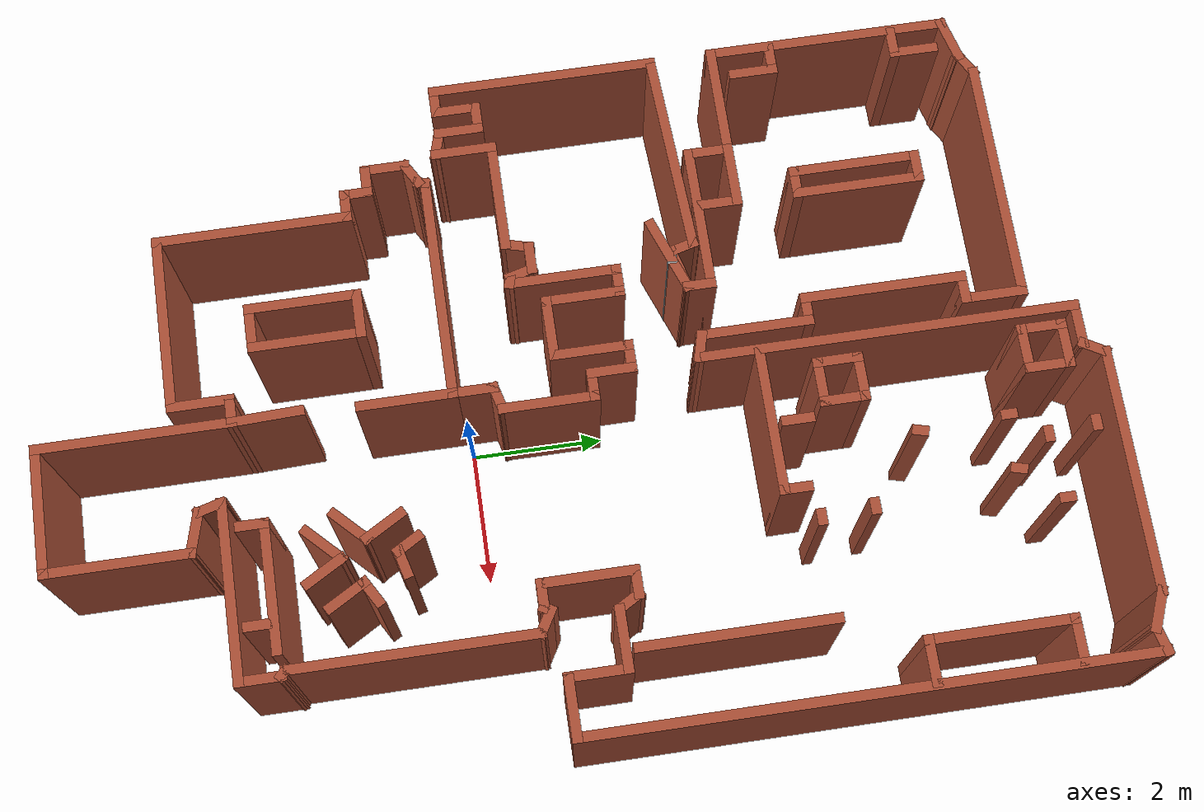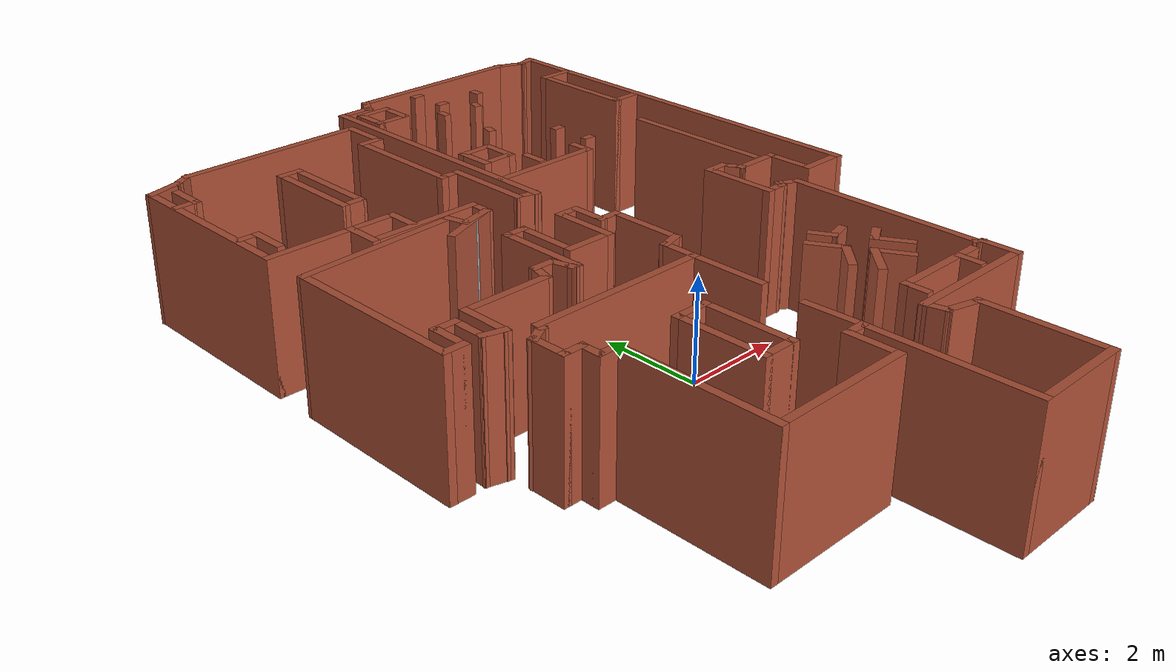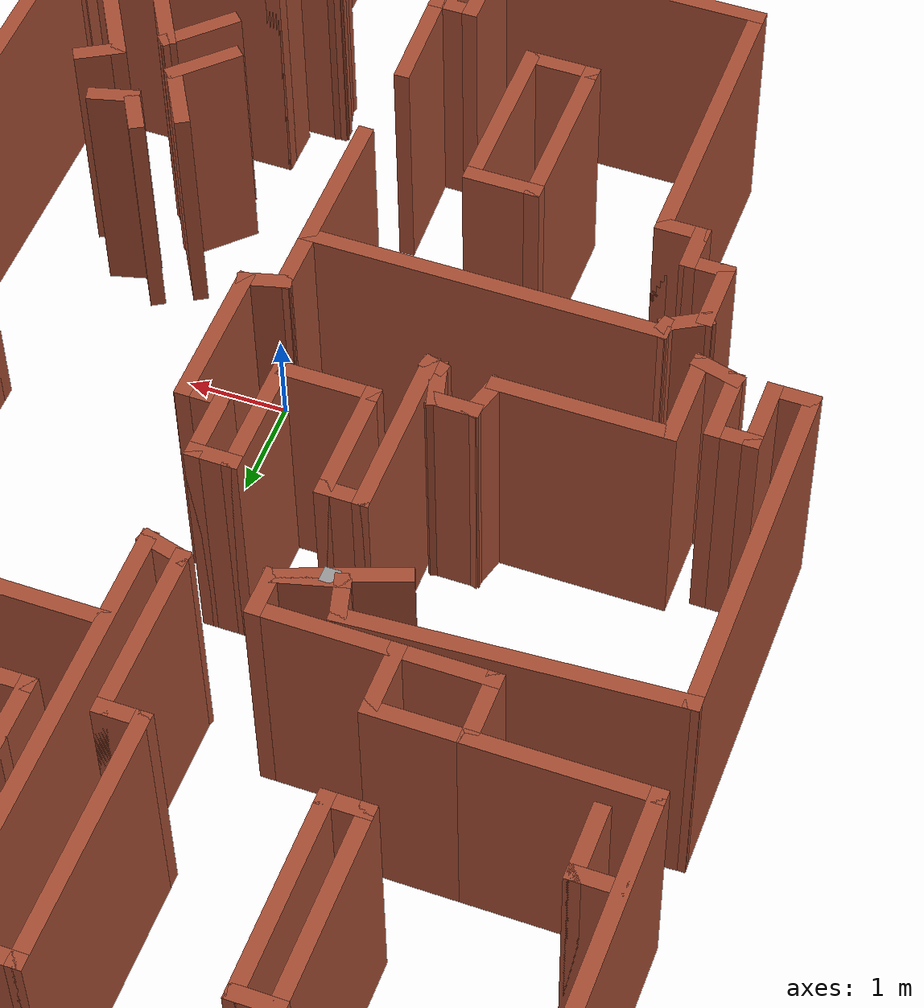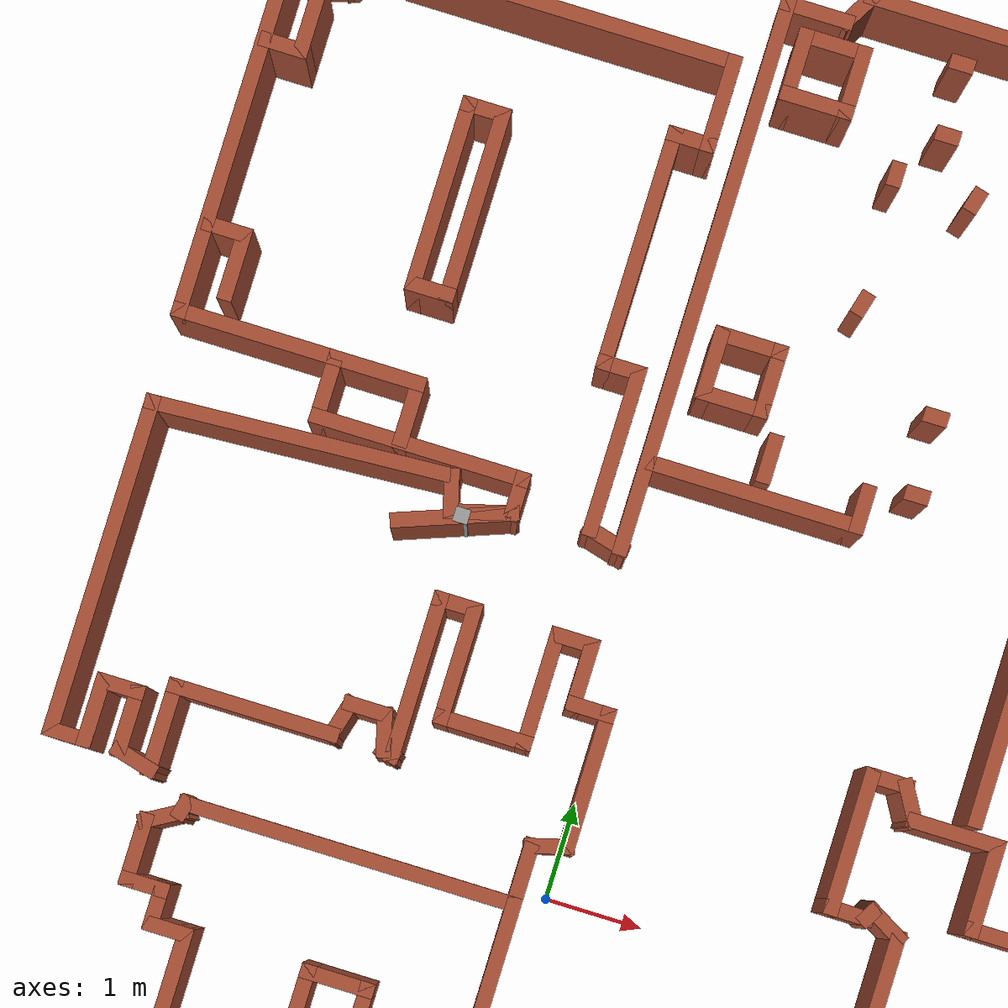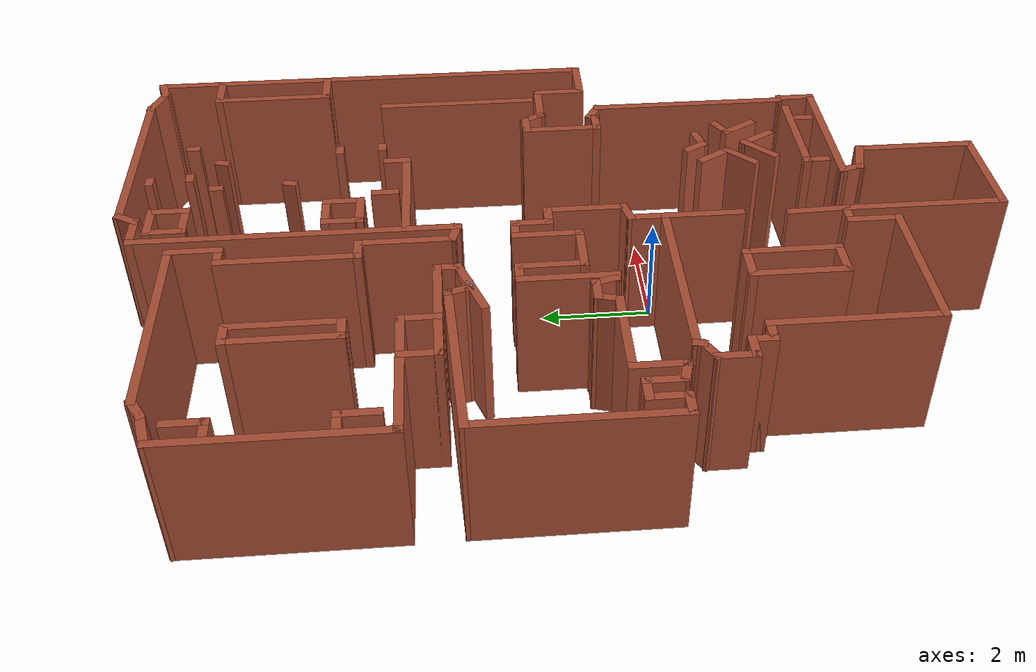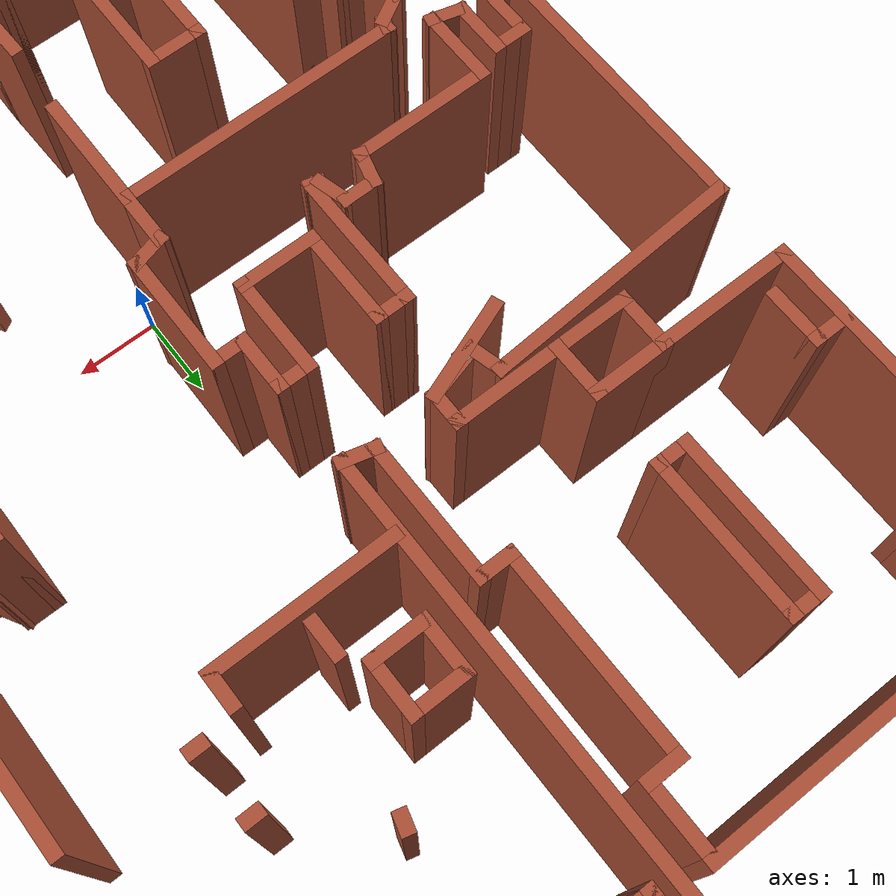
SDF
<?xml version='1.0'?>
<sdf version='1.6'>
  <model name='map_26'>
    <pose frame=''>-0.123106 1.60816 0 0 -0 0</pose>
    <link name='Wall_1'>
      <collision name='Wall_1_Collision'>
        <geometry>
          <box>
            <size>3.75 0.15 2.5</size>
          </box>
        </geometry>
        <pose frame=''>0 0 1.25 0 -0 0</pose>
      </collision>
      <visual name='Wall_1_Visual'>
        <pose frame=''>0 0 1.25 0 -0 0</pose>
        <geometry>
          <box>
            <size>3.75 0.15 2.5</size>
          </box>
        </geometry>
        <material>
          <script>
            <uri>file://media/materials/scripts/gazebo.material</uri>
            <name>Gazebo/Bricks</name>
          </script>
          <ambient>1 1 1 1</ambient>
        </material>
        <meta>
          <layer>0</layer>
        </meta>
      </visual>
      <pose frame=''>2.37487 7.7923 0 0 -0 3.14159</pose>
    </link>
    <link name='Wall_10'>
      <collision name='Wall_10_Collision'>
        <geometry>
          <box>
            <size>1 0.15 2.5</size>
          </box>
        </geometry>
        <pose frame=''>0 0 1.25 0 -0 0</pose>
      </collision>
      <visual name='Wall_10_Visual'>
        <pose frame=''>0 0 1.25 0 -0 0</pose>
        <geometry>
          <box>
            <size>1 0.15 2.5</size>
          </box>
        </geometry>
        <material>
          <script>
            <uri>file://media/materials/scripts/gazebo.material</uri>
            <name>Gazebo/Bricks</name>
          </script>
          <ambient>1 1 1 1</ambient>
        </material>
        <meta>
          <layer>0</layer>
        </meta>
      </visual>
      <pose frame=''>-0.538205 6.35478 0 0 -0 1.5708</pose>
    </link>
    <link name='Wall_101'>
      <collision name='Wall_101_Collision'>
        <geometry>
          <box>
            <size>0.75 0.15 2.5</size>
          </box>
        </geometry>
        <pose frame=''>0 0 1.25 0 -0 0</pose>
      </collision>
      <visual name='Wall_101_Visual'>
        <pose frame=''>0 0 1.25 0 -0 0</pose>
        <geometry>
          <box>
            <size>0.75 0.15 2.5</size>
          </box>
        </geometry>
        <material>
          <script>
            <uri>file://media/materials/scripts/gazebo.material</uri>
            <name>Gazebo/Bricks</name>
          </script>
          <ambient>1 1 1 1</ambient>
        </material>
        <meta>
          <layer>0</layer>
        </meta>
      </visual>
      <pose frame=''>-4.63789 5.94255 0 0 -0 -1.5708</pose>
    </link>
    <link name='Wall_102'>
      <collision name='Wall_102_Collision'>
        <geometry>
          <box>
            <size>0.5 0.15 2.5</size>
          </box>
        </geometry>
        <pose frame=''>0 0 1.25 0 -0 0</pose>
      </collision>
      <visual name='Wall_102_Visual'>
        <pose frame=''>0 0 1.25 0 -0 0</pose>
        <geometry>
          <box>
            <size>0.5 0.15 2.5</size>
          </box>
        </geometry>
        <material>
          <script>
            <uri>file://media/materials/scripts/gazebo.material</uri>
            <name>Gazebo/Bricks</name>
          </script>
          <ambient>1 1 1 1</ambient>
        </material>
        <meta>
          <layer>0</layer>
        </meta>
      </visual>
      <pose frame=''>-4.81289 5.64255 0 0 -0 3.14159</pose>
    </link>
    <link name='Wall_106'>
      <collision name='Wall_106_Collision'>
        <geometry>
          <box>
            <size>0.5 0.15 2.5</size>
          </box>
        </geometry>
        <pose frame=''>0 0 1.25 0 -0 0</pose>
      </collision>
      <visual name='Wall_106_Visual'>
        <pose frame=''>0 0 1.25 0 -0 0</pose>
        <geometry>
          <box>
            <size>0.5 0.15 2.5</size>
          </box>
        </geometry>
        <material>
          <script>
            <uri>file://media/materials/scripts/gazebo.material</uri>
            <name>Gazebo/Bricks</name>
          </script>
          <ambient>1 1 1 1</ambient>
        </material>
        <meta>
          <layer>0</layer>
        </meta>
      </visual>
      <pose frame=''>-4.80985 3.74444 0 0 -0 0</pose>
    </link>
    <link name='Wall_107'>
      <collision name='Wall_107_Collision'>
        <geometry>
          <box>
            <size>0.75 0.15 2.5</size>
          </box>
        </geometry>
        <pose frame=''>0 0 1.25 0 -0 0</pose>
      </collision>
      <visual name='Wall_107_Visual'>
        <pose frame=''>0 0 1.25 0 -0 0</pose>
        <geometry>
          <box>
            <size>0.75 0.15 2.5</size>
          </box>
        </geometry>
        <material>
          <script>
            <uri>file://media/materials/scripts/gazebo.material</uri>
            <name>Gazebo/Bricks</name>
          </script>
          <ambient>1 1 1 1</ambient>
        </material>
        <meta>
          <layer>0</layer>
        </meta>
      </visual>
      <pose frame=''>-4.63485 3.44444 0 0 -0 -1.5708</pose>
    </link>
    <link name='Wall_109'>
      <collision name='Wall_109_Collision'>
        <geometry>
          <box>
            <size>0.5 0.15 2.5</size>
          </box>
        </geometry>
        <pose frame=''>0 0 1.25 0 -0 0</pose>
      </collision>
      <visual name='Wall_109_Visual'>
        <pose frame=''>0 0 1.25 0 -0 0</pose>
        <geometry>
          <box>
            <size>0.5 0.15 2.5</size>
          </box>
        </geometry>
        <material>
          <script>
            <uri>file://media/materials/scripts/gazebo.material</uri>
            <name>Gazebo/Bricks</name>
          </script>
          <ambient>1 1 1 1</ambient>
        </material>
        <meta>
          <layer>0</layer>
        </meta>
      </visual>
      <pose frame=''>-2.73114 5.61802 0 0 -0 3.14159</pose>
    </link>
    <link name='Wall_11'>
      <collision name='Wall_11_Collision'>
        <geometry>
          <box>
            <size>3.75 0.15 2.5</size>
          </box>
        </geometry>
        <pose frame=''>0 0 1.25 0 -0 0</pose>
      </collision>
      <visual name='Wall_11_Visual'>
        <pose frame=''>0 0 1.25 0 -0 0</pose>
        <geometry>
          <box>
            <size>3.75 0.15 2.5</size>
          </box>
        </geometry>
        <material>
          <script>
            <uri>file://media/materials/scripts/gazebo.material</uri>
            <name>Gazebo/Bricks</name>
          </script>
          <ambient>1 1 1 1</ambient>
        </material>
        <meta>
          <layer>0</layer>
        </meta>
      </visual>
      <pose frame=''>-2.3382 6.77978 0 0 -0 3.14159</pose>
    </link>
    <link name='Wall_110'>
      <collision name='Wall_110_Collision'>
        <geometry>
          <box>
            <size>2 0.15 2.5</size>
          </box>
        </geometry>
        <pose frame=''>0 0 1.25 0 -0 0</pose>
      </collision>
      <visual name='Wall_110_Visual'>
        <pose frame=''>0 0 1.25 0 -0 0</pose>
        <geometry>
          <box>
            <size>2 0.15 2.5</size>
          </box>
        </geometry>
        <material>
          <script>
            <uri>file://media/materials/scripts/gazebo.material</uri>
            <name>Gazebo/Bricks</name>
          </script>
          <ambient>1 1 1 1</ambient>
        </material>
        <meta>
          <layer>0</layer>
        </meta>
      </visual>
      <pose frame=''>-2.90614 4.69302 0 0 -0 -1.5708</pose>
    </link>
    <link name='Wall_111'>
      <collision name='Wall_111_Collision'>
        <geometry>
          <box>
            <size>0.5 0.15 2.5</size>
          </box>
        </geometry>
        <pose frame=''>0 0 1.25 0 -0 0</pose>
      </collision>
      <visual name='Wall_111_Visual'>
        <pose frame=''>0 0 1.25 0 -0 0</pose>
        <geometry>
          <box>
            <size>0.5 0.15 2.5</size>
          </box>
        </geometry>
        <material>
          <script>
            <uri>file://media/materials/scripts/gazebo.material</uri>
            <name>Gazebo/Bricks</name>
          </script>
          <ambient>1 1 1 1</ambient>
        </material>
        <meta>
          <layer>0</layer>
        </meta>
      </visual>
      <pose frame=''>-2.73114 3.76802 0 0 -0 0</pose>
    </link>
    <link name='Wall_113'>
      <collision name='Wall_113_Collision'>
        <geometry>
          <box>
            <size>2 0.15 2.5</size>
          </box>
        </geometry>
        <pose frame=''>0 0 1.25 0 -0 0</pose>
      </collision>
      <visual name='Wall_113_Visual'>
        <pose frame=''>0 0 1.25 0 -0 0</pose>
        <geometry>
          <box>
            <size>2 0.15 2.5</size>
          </box>
        </geometry>
        <material>
          <script>
            <uri>file://media/materials/scripts/gazebo.material</uri>
            <name>Gazebo/Bricks</name>
          </script>
          <ambient>1 1 1 1</ambient>
        </material>
        <meta>
          <layer>0</layer>
        </meta>
      </visual>
      <pose frame=''>-2.55614 4.69302 0 0 -0 -1.5708</pose>
    </link>
    <link name='Wall_115'>
      <collision name='Wall_115_Collision'>
        <geometry>
          <box>
            <size>1 0.15 2.5</size>
          </box>
        </geometry>
        <pose frame=''>0 0 1.25 0 -0 0</pose>
      </collision>
      <visual name='Wall_115_Visual'>
        <pose frame=''>0 0 1.25 0 -0 0</pose>
        <geometry>
          <box>
            <size>1 0.15 2.5</size>
          </box>
        </geometry>
        <material>
          <script>
            <uri>file://media/materials/scripts/gazebo.material</uri>
            <name>Gazebo/Bricks</name>
          </script>
          <ambient>1 1 1 1</ambient>
        </material>
        <meta>
          <layer>0</layer>
        </meta>
      </visual>
      <pose frame=''>-2.99587 2.84949 0 0 -0 0</pose>
    </link>
    <link name='Wall_116'>
      <collision name='Wall_116_Collision'>
        <geometry>
          <box>
            <size>0.75 0.15 2.5</size>
          </box>
        </geometry>
        <pose frame=''>0 0 1.25 0 -0 0</pose>
      </collision>
      <visual name='Wall_116_Visual'>
        <pose frame=''>0 0 1.25 0 -0 0</pose>
        <geometry>
          <box>
            <size>0.75 0.15 2.5</size>
          </box>
        </geometry>
        <material>
          <script>
            <uri>file://media/materials/scripts/gazebo.material</uri>
            <name>Gazebo/Bricks</name>
          </script>
          <ambient>1 1 1 1</ambient>
        </material>
        <meta>
          <layer>0</layer>
        </meta>
      </visual>
      <pose frame=''>-2.57087 2.54948 0 0 -0 -1.5708</pose>
    </link>
    <link name='Wall_118'>
      <collision name='Wall_118_Collision'>
        <geometry>
          <box>
            <size>0.75 0.15 2.5</size>
          </box>
        </geometry>
        <pose frame=''>0 0 1.25 0 -0 0</pose>
      </collision>
      <visual name='Wall_118_Visual'>
        <pose frame=''>0 0 1.25 0 -0 0</pose>
        <geometry>
          <box>
            <size>0.75 0.15 2.5</size>
          </box>
        </geometry>
        <material>
          <script>
            <uri>file://media/materials/scripts/gazebo.material</uri>
            <name>Gazebo/Bricks</name>
          </script>
          <ambient>1 1 1 1</ambient>
        </material>
        <meta>
          <layer>0</layer>
        </meta>
      </visual>
      <pose frame=''>4.68444 6.49698 0 0 -0 3.14159</pose>
    </link>
    <link name='Wall_119'>
      <collision name='Wall_119_Collision'>
        <geometry>
          <box>
            <size>2.25 0.15 2.5</size>
          </box>
        </geometry>
        <pose frame=''>0 0 1.25 0 -0 0</pose>
      </collision>
      <visual name='Wall_119_Visual'>
        <pose frame=''>0 0 1.25 0 -0 0</pose>
        <geometry>
          <box>
            <size>2.25 0.15 2.5</size>
          </box>
        </geometry>
        <material>
          <script>
            <uri>file://media/materials/scripts/gazebo.material</uri>
            <name>Gazebo/Bricks</name>
          </script>
          <ambient>1 1 1 1</ambient>
        </material>
        <meta>
          <layer>0</layer>
        </meta>
      </visual>
      <pose frame=''>4.38444 5.44698 0 0 -0 -1.5708</pose>
    </link>
    <link name='Wall_12'>
      <collision name='Wall_12_Collision'>
        <geometry>
          <box>
            <size>0.5 0.15 2.5</size>
          </box>
        </geometry>
        <pose frame=''>0 0 1.25 0 -0 0</pose>
      </collision>
      <visual name='Wall_12_Visual'>
        <pose frame=''>0 0 1.25 0 -0 0</pose>
        <geometry>
          <box>
            <size>0.5 0.15 2.5</size>
          </box>
        </geometry>
        <material>
          <script>
            <uri>file://media/materials/scripts/gazebo.material</uri>
            <name>Gazebo/Bricks</name>
          </script>
          <ambient>1 1 1 1</ambient>
        </material>
        <meta>
          <layer>0</layer>
        </meta>
      </visual>
      <pose frame=''>-4.28976 6.69228 0 0 -0 -2.61799</pose>
    </link>
    <link name='Wall_120'>
      <collision name='Wall_120_Collision'>
        <geometry>
          <box>
            <size>0.75 0.15 2.5</size>
          </box>
        </geometry>
        <pose frame=''>0 0 1.25 0 -0 0</pose>
      </collision>
      <visual name='Wall_120_Visual'>
        <pose frame=''>0 0 1.25 0 -0 0</pose>
        <geometry>
          <box>
            <size>0.75 0.15 2.5</size>
          </box>
        </geometry>
        <material>
          <script>
            <uri>file://media/materials/scripts/gazebo.material</uri>
            <name>Gazebo/Bricks</name>
          </script>
          <ambient>1 1 1 1</ambient>
        </material>
        <meta>
          <layer>0</layer>
        </meta>
      </visual>
      <pose frame=''>4.68444 4.39698 0 0 -0 0</pose>
    </link>
    <link name='Wall_122'>
      <collision name='Wall_122_Collision'>
        <geometry>
          <box>
            <size>2.25 0.15 2.5</size>
          </box>
        </geometry>
        <pose frame=''>0 0 1.25 0 -0 0</pose>
      </collision>
      <visual name='Wall_122_Visual'>
        <pose frame=''>0 0 1.25 0 -0 0</pose>
        <geometry>
          <box>
            <size>2.25 0.15 2.5</size>
          </box>
        </geometry>
        <material>
          <script>
            <uri>file://media/materials/scripts/gazebo.material</uri>
            <name>Gazebo/Bricks</name>
          </script>
          <ambient>1 1 1 1</ambient>
        </material>
        <meta>
          <layer>0</layer>
        </meta>
      </visual>
      <pose frame=''>0.899445 2.77296 0 0 -0 0</pose>
    </link>
    <link name='Wall_123'>
      <collision name='Wall_123_Collision'>
        <geometry>
          <box>
            <size>0.5 0.15 2.5</size>
          </box>
        </geometry>
        <pose frame=''>0 0 1.25 0 -0 0</pose>
      </collision>
      <visual name='Wall_123_Visual'>
        <pose frame=''>0 0 1.25 0 -0 0</pose>
        <geometry>
          <box>
            <size>0.5 0.15 2.5</size>
          </box>
        </geometry>
        <material>
          <script>
            <uri>file://media/materials/scripts/gazebo.material</uri>
            <name>Gazebo/Bricks</name>
          </script>
          <ambient>1 1 1 1</ambient>
        </material>
        <meta>
          <layer>0</layer>
        </meta>
      </visual>
      <pose frame=''>1.94945 2.94796 0 0 -0 1.5708</pose>
    </link>
    <link name='Wall_125'>
      <collision name='Wall_125_Collision'>
        <geometry>
          <box>
            <size>0.5 0.15 2.5</size>
          </box>
        </geometry>
        <pose frame=''>0 0 1.25 0 -0 0</pose>
      </collision>
      <visual name='Wall_125_Visual'>
        <pose frame=''>0 0 1.25 0 -0 0</pose>
        <geometry>
          <box>
            <size>0.5 0.15 2.5</size>
          </box>
        </geometry>
        <material>
          <script>
            <uri>file://media/materials/scripts/gazebo.material</uri>
            <name>Gazebo/Bricks</name>
          </script>
          <ambient>1 1 1 1</ambient>
        </material>
        <meta>
          <layer>0</layer>
        </meta>
      </visual>
      <pose frame=''>0.936584 3.15309 0 0 -0 -1.5708</pose>
    </link>
    <link name='Wall_128'>
      <collision name='Wall_128_Collision'>
        <geometry>
          <box>
            <size>0.75 0.15 2.5</size>
          </box>
        </geometry>
        <pose frame=''>0 0 1.25 0 -0 0</pose>
      </collision>
      <visual name='Wall_128_Visual'>
        <pose frame=''>0 0 1.25 0 -0 0</pose>
        <geometry>
          <box>
            <size>0.75 0.15 2.5</size>
          </box>
        </geometry>
        <material>
          <script>
            <uri>file://media/materials/scripts/gazebo.material</uri>
            <name>Gazebo/Bricks</name>
          </script>
          <ambient>1 1 1 1</ambient>
        </material>
        <meta>
          <layer>0</layer>
        </meta>
      </visual>
      <pose frame=''>0.057621 6.93716 0 0 -0 -1.5708</pose>
    </link>
    <link name='Wall_129'>
      <collision name='Wall_129_Collision'>
        <geometry>
          <box>
            <size>0.75 0.15 2.5</size>
          </box>
        </geometry>
        <pose frame=''>0 0 1.25 0 -0 0</pose>
      </collision>
      <visual name='Wall_129_Visual'>
        <pose frame=''>0 0 1.25 0 -0 0</pose>
        <geometry>
          <box>
            <size>0.75 0.15 2.5</size>
          </box>
        </geometry>
        <material>
          <script>
            <uri>file://media/materials/scripts/gazebo.material</uri>
            <name>Gazebo/Bricks</name>
          </script>
          <ambient>1 1 1 1</ambient>
        </material>
        <meta>
          <layer>0</layer>
        </meta>
      </visual>
      <pose frame=''>0.357621 6.63716 0 0 -0 0</pose>
    </link>
    <link name='Wall_13'>
      <collision name='Wall_13_Collision'>
        <geometry>
          <box>
            <size>0.75 0.15 2.5</size>
          </box>
        </geometry>
        <pose frame=''>0 0 1.25 0 -0 0</pose>
      </collision>
      <visual name='Wall_13_Visual'>
        <pose frame=''>0 0 1.25 0 -0 0</pose>
        <geometry>
          <box>
            <size>0.75 0.15 2.5</size>
          </box>
        </geometry>
        <material>
          <script>
            <uri>file://media/materials/scripts/gazebo.material</uri>
            <name>Gazebo/Bricks</name>
          </script>
          <ambient>1 1 1 1</ambient>
        </material>
        <meta>
          <layer>0</layer>
        </meta>
      </visual>
      <pose frame=''>-4.73109 6.52713 0 0 -0 -2.87979</pose>
    </link>
    <link name='Wall_130'>
      <collision name='Wall_130_Collision'>
        <geometry>
          <box>
            <size>0.75 0.15 2.5</size>
          </box>
        </geometry>
        <pose frame=''>0 0 1.25 0 -0 0</pose>
      </collision>
      <visual name='Wall_130_Visual'>
        <pose frame=''>0 0 1.25 0 -0 0</pose>
        <geometry>
          <box>
            <size>0.75 0.15 2.5</size>
          </box>
        </geometry>
        <material>
          <script>
            <uri>file://media/materials/scripts/gazebo.material</uri>
            <name>Gazebo/Bricks</name>
          </script>
          <ambient>1 1 1 1</ambient>
        </material>
        <meta>
          <layer>0</layer>
        </meta>
      </visual>
      <pose frame=''>0.657621 6.93716 0 0 -0 1.5708</pose>
    </link>
    <link name='Wall_131'>
      <collision name='Wall_131_Collision'>
        <geometry>
          <box>
            <size>0.75 0.15 2.5</size>
          </box>
        </geometry>
        <pose frame=''>0 0 1.25 0 -0 0</pose>
      </collision>
      <visual name='Wall_131_Visual'>
        <pose frame=''>0 0 1.25 0 -0 0</pose>
        <geometry>
          <box>
            <size>0.75 0.15 2.5</size>
          </box>
        </geometry>
        <material>
          <script>
            <uri>file://media/materials/scripts/gazebo.material</uri>
            <name>Gazebo/Bricks</name>
          </script>
          <ambient>1 1 1 1</ambient>
        </material>
        <meta>
          <layer>0</layer>
        </meta>
      </visual>
      <pose frame=''>0.357621 7.23716 0 0 -0 3.14159</pose>
    </link>
    <link name='Wall_135'>
      <collision name='Wall_135_Collision'>
        <geometry>
          <box>
            <size>0.75 0.15 2.5</size>
          </box>
        </geometry>
        <pose frame=''>0 0 1.25 0 -0 0</pose>
      </collision>
      <visual name='Wall_135_Visual'>
        <pose frame=''>0 0 1.25 0 -0 0</pose>
        <geometry>
          <box>
            <size>0.75 0.15 2.5</size>
          </box>
        </geometry>
        <material>
          <script>
            <uri>file://media/materials/scripts/gazebo.material</uri>
            <name>Gazebo/Bricks</name>
          </script>
          <ambient>1 1 1 1</ambient>
        </material>
        <meta>
          <layer>0</layer>
        </meta>
      </visual>
      <pose frame=''>0.127013 3.88392 0 0 -0 -1.5708</pose>
    </link>
    <link name='Wall_136'>
      <collision name='Wall_136_Collision'>
        <geometry>
          <box>
            <size>0.75 0.15 2.5</size>
          </box>
        </geometry>
        <pose frame=''>0 0 1.25 0 -0 0</pose>
      </collision>
      <visual name='Wall_136_Visual'>
        <pose frame=''>0 0 1.25 0 -0 0</pose>
        <geometry>
          <box>
            <size>0.75 0.15 2.5</size>
          </box>
        </geometry>
        <material>
          <script>
            <uri>file://media/materials/scripts/gazebo.material</uri>
            <name>Gazebo/Bricks</name>
          </script>
          <ambient>1 1 1 1</ambient>
        </material>
        <meta>
          <layer>0</layer>
        </meta>
      </visual>
      <pose frame=''>0.427013 3.58392 0 0 -0 0</pose>
    </link>
    <link name='Wall_137'>
      <collision name='Wall_137_Collision'>
        <geometry>
          <box>
            <size>0.75 0.15 2.5</size>
          </box>
        </geometry>
        <pose frame=''>0 0 1.25 0 -0 0</pose>
      </collision>
      <visual name='Wall_137_Visual'>
        <pose frame=''>0 0 1.25 0 -0 0</pose>
        <geometry>
          <box>
            <size>0.75 0.15 2.5</size>
          </box>
        </geometry>
        <material>
          <script>
            <uri>file://media/materials/scripts/gazebo.material</uri>
            <name>Gazebo/Bricks</name>
          </script>
          <ambient>1 1 1 1</ambient>
        </material>
        <meta>
          <layer>0</layer>
        </meta>
      </visual>
      <pose frame=''>0.727013 3.88392 0 0 -0 1.5708</pose>
    </link>
    <link name='Wall_138'>
      <collision name='Wall_138_Collision'>
        <geometry>
          <box>
            <size>0.75 0.15 2.5</size>
          </box>
        </geometry>
        <pose frame=''>0 0 1.25 0 -0 0</pose>
      </collision>
      <visual name='Wall_138_Visual'>
        <pose frame=''>0 0 1.25 0 -0 0</pose>
        <geometry>
          <box>
            <size>0.75 0.15 2.5</size>
          </box>
        </geometry>
        <material>
          <script>
            <uri>file://media/materials/scripts/gazebo.material</uri>
            <name>Gazebo/Bricks</name>
          </script>
          <ambient>1 1 1 1</ambient>
        </material>
        <meta>
          <layer>0</layer>
        </meta>
      </visual>
      <pose frame=''>0.427013 4.18392 0 0 -0 3.14159</pose>
    </link>
    <link name='Wall_14'>
      <collision name='Wall_14_Collision'>
        <geometry>
          <box>
            <size>3.75 0.15 2.5</size>
          </box>
        </geometry>
        <pose frame=''>0 0 1.25 0 -0 0</pose>
      </collision>
      <visual name='Wall_14_Visual'>
        <pose frame=''>0 0 1.25 0 -0 0</pose>
        <geometry>
          <box>
            <size>3.75 0.15 2.5</size>
          </box>
        </geometry>
        <material>
          <script>
            <uri>file://media/materials/scripts/gazebo.material</uri>
            <name>Gazebo/Bricks</name>
          </script>
          <ambient>1 1 1 1</ambient>
        </material>
        <meta>
          <layer>0</layer>
        </meta>
      </visual>
      <pose frame=''>-5.02087 4.64949 0 0 -0 -1.5708</pose>
    </link>
    <link name='Wall_140'>
      <collision name='Wall_140_Collision'>
        <geometry>
          <box>
            <size>3 0.15 2.5</size>
          </box>
        </geometry>
        <pose frame=''>0 0 1.25 0 -0 0</pose>
      </collision>
      <visual name='Wall_140_Visual'>
        <pose frame=''>0 0 1.25 0 -0 0</pose>
        <geometry>
          <box>
            <size>3 0.15 2.5</size>
          </box>
        </geometry>
        <material>
          <script>
            <uri>file://media/materials/scripts/gazebo.material</uri>
            <name>Gazebo/Bricks</name>
          </script>
          <ambient>1 1 1 1</ambient>
        </material>
        <meta>
          <layer>0</layer>
        </meta>
      </visual>
      <pose frame=''>3.8973 1.78744 0 0 -0 -1.5708</pose>
    </link>
    <link name='Wall_147'>
      <collision name='Wall_147_Collision'>
        <geometry>
          <box>
            <size>1.75 0.15 2.5</size>
          </box>
        </geometry>
        <pose frame=''>0 0 1.25 0 -0 0</pose>
      </collision>
      <visual name='Wall_147_Visual'>
        <pose frame=''>0 0 1.25 0 -0 0</pose>
        <geometry>
          <box>
            <size>1.75 0.15 2.5</size>
          </box>
        </geometry>
        <material>
          <script>
            <uri>file://media/materials/scripts/gazebo.material</uri>
            <name>Gazebo/Bricks</name>
          </script>
          <ambient>1 1 1 1</ambient>
        </material>
        <meta>
          <layer>0</layer>
        </meta>
      </visual>
      <pose frame=''>-1.90848 -3.76343 0 0 -0 -1.5708</pose>
    </link>
    <link name='Wall_148'>
      <collision name='Wall_148_Collision'>
        <geometry>
          <box>
            <size>0.75 0.15 2.5</size>
          </box>
        </geometry>
        <pose frame=''>0 0 1.25 0 -0 0</pose>
      </collision>
      <visual name='Wall_148_Visual'>
        <pose frame=''>0 0 1.25 0 -0 0</pose>
        <geometry>
          <box>
            <size>0.75 0.15 2.5</size>
          </box>
        </geometry>
        <material>
          <script>
            <uri>file://media/materials/scripts/gazebo.material</uri>
            <name>Gazebo/Bricks</name>
          </script>
          <ambient>1 1 1 1</ambient>
        </material>
        <meta>
          <layer>0</layer>
        </meta>
      </visual>
      <pose frame=''>-1.60848 -4.56343 0 0 -0 0</pose>
    </link>
    <link name='Wall_149'>
      <collision name='Wall_149_Collision'>
        <geometry>
          <box>
            <size>1.75 0.15 2.5</size>
          </box>
        </geometry>
        <pose frame=''>0 0 1.25 0 -0 0</pose>
      </collision>
      <visual name='Wall_149_Visual'>
        <pose frame=''>0 0 1.25 0 -0 0</pose>
        <geometry>
          <box>
            <size>1.75 0.15 2.5</size>
          </box>
        </geometry>
        <material>
          <script>
            <uri>file://media/materials/scripts/gazebo.material</uri>
            <name>Gazebo/Bricks</name>
          </script>
          <ambient>1 1 1 1</ambient>
        </material>
        <meta>
          <layer>0</layer>
        </meta>
      </visual>
      <pose frame=''>-1.30848 -3.76343 0 0 -0 1.5708</pose>
    </link>
    <link name='Wall_15'>
      <collision name='Wall_15_Collision'>
        <geometry>
          <box>
            <size>1.75 0.15 2.5</size>
          </box>
        </geometry>
        <pose frame=''>0 0 1.25 0 -0 0</pose>
      </collision>
      <visual name='Wall_15_Visual'>
        <pose frame=''>0 0 1.25 0 -0 0</pose>
        <geometry>
          <box>
            <size>1.75 0.15 2.5</size>
          </box>
        </geometry>
        <material>
          <script>
            <uri>file://media/materials/scripts/gazebo.material</uri>
            <name>Gazebo/Bricks</name>
          </script>
          <ambient>1 1 1 1</ambient>
        </material>
        <meta>
          <layer>0</layer>
        </meta>
      </visual>
      <pose frame=''>-4.22087 2.84949 0 0 -0 0</pose>
    </link>
    <link name='Wall_150'>
      <collision name='Wall_150_Collision'>
        <geometry>
          <box>
            <size>0.75 0.15 2.5</size>
          </box>
        </geometry>
        <pose frame=''>0 0 1.25 0 -0 0</pose>
      </collision>
      <visual name='Wall_150_Visual'>
        <pose frame=''>0 0 1.25 0 -0 0</pose>
        <geometry>
          <box>
            <size>0.75 0.15 2.5</size>
          </box>
        </geometry>
        <material>
          <script>
            <uri>file://media/materials/scripts/gazebo.material</uri>
            <name>Gazebo/Bricks</name>
          </script>
          <ambient>1 1 1 1</ambient>
        </material>
        <meta>
          <layer>0</layer>
        </meta>
      </visual>
      <pose frame=''>-1.60848 -2.96343 0 0 -0 -3.14159</pose>
    </link>
    <link name='Wall_152'>
      <collision name='Wall_152_Collision'>
        <geometry>
          <box>
            <size>1.5 0.15 2.5</size>
          </box>
        </geometry>
        <pose frame=''>0 0 1.25 0 -0 0</pose>
      </collision>
      <visual name='Wall_152_Visual'>
        <pose frame=''>0 0 1.25 0 -0 0</pose>
        <geometry>
          <box>
            <size>1.5 0.15 2.5</size>
          </box>
        </geometry>
        <material>
          <script>
            <uri>file://media/materials/scripts/gazebo.material</uri>
            <name>Gazebo/Bricks</name>
          </script>
          <ambient>1 1 1 1</ambient>
        </material>
        <meta>
          <layer>0</layer>
        </meta>
      </visual>
      <pose frame=''>-0.181178 -2.42316 0 0 -0 -1.5708</pose>
    </link>
    <link name='Wall_154'>
      <collision name='Wall_154_Collision'>
        <geometry>
          <box>
            <size>1.13912 0.15 2.5</size>
          </box>
        </geometry>
        <pose frame=''>0 0 1.25 0 -0 0</pose>
      </collision>
      <visual name='Wall_154_Visual'>
        <pose frame=''>0 0 1.25 0 -0 0</pose>
        <geometry>
          <box>
            <size>1.13912 0.15 2.5</size>
          </box>
        </geometry>
        <material>
          <script>
            <uri>file://media/materials/scripts/gazebo.material</uri>
            <name>Gazebo/Bricks</name>
          </script>
          <ambient>1 1 1 1</ambient>
        </material>
        <meta>
          <layer>0</layer>
        </meta>
      </visual>
      <pose frame=''>-0.226623 -4.47546 0 0 -0 -1.53752</pose>
    </link>
    <link name='Wall_156'>
      <collision name='Wall_156_Collision'>
        <geometry>
          <box>
            <size>2 0.15 2.5</size>
          </box>
        </geometry>
        <pose frame=''>0 0 1.25 0 -0 0</pose>
      </collision>
      <visual name='Wall_156_Visual'>
        <pose frame=''>0 0 1.25 0 -0 0</pose>
        <geometry>
          <box>
            <size>2 0.15 2.5</size>
          </box>
        </geometry>
        <material>
          <script>
            <uri>file://media/materials/scripts/gazebo.material</uri>
            <name>Gazebo/Bricks</name>
          </script>
          <ambient>1 1 1 1</ambient>
        </material>
        <meta>
          <layer>0</layer>
        </meta>
      </visual>
      <pose frame=''>2.27793 -4.65197 0 0 -0 0</pose>
    </link>
    <link name='Wall_160'>
      <collision name='Wall_160_Collision'>
        <geometry>
          <box>
            <size>0.5 0.15 2.5</size>
          </box>
        </geometry>
        <pose frame=''>0 0 1.25 0 -0 0</pose>
      </collision>
      <visual name='Wall_160_Visual'>
        <pose frame=''>0 0 1.25 0 -0 0</pose>
        <geometry>
          <box>
            <size>0.5 0.15 2.5</size>
          </box>
        </geometry>
        <material>
          <script>
            <uri>file://media/materials/scripts/gazebo.material</uri>
            <name>Gazebo/Bricks</name>
          </script>
          <ambient>1 1 1 1</ambient>
        </material>
        <meta>
          <layer>0</layer>
        </meta>
      </visual>
      <pose frame=''>1.35293 -4.82697 0 0 -0 -1.5708</pose>
    </link>
    <link name='Wall_162'>
      <collision name='Wall_162_Collision'>
        <geometry>
          <box>
            <size>0.5 0.15 2.5</size>
          </box>
        </geometry>
        <pose frame=''>0 0 1.25 0 -0 0</pose>
      </collision>
      <visual name='Wall_162_Visual'>
        <pose frame=''>0 0 1.25 0 -0 0</pose>
        <geometry>
          <box>
            <size>0.5 0.15 2.5</size>
          </box>
        </geometry>
        <material>
          <script>
            <uri>file://media/materials/scripts/gazebo.material</uri>
            <name>Gazebo/Bricks</name>
          </script>
          <ambient>1 1 1 1</ambient>
        </material>
        <meta>
          <layer>0</layer>
        </meta>
      </visual>
      <pose frame=''>2.81016 -4.8501 0 0 -0 -1.5708</pose>
    </link>
    <link name='Wall_164'>
      <collision name='Wall_164_Collision'>
        <geometry>
          <box>
            <size>0.5 0.15 2.5</size>
          </box>
        </geometry>
        <pose frame=''>0 0 1.25 0 -0 0</pose>
      </collision>
      <visual name='Wall_164_Visual'>
        <pose frame=''>0 0 1.25 0 -0 0</pose>
        <geometry>
          <box>
            <size>0.5 0.15 2.5</size>
          </box>
        </geometry>
        <material>
          <script>
            <uri>file://media/materials/scripts/gazebo.material</uri>
            <name>Gazebo/Bricks</name>
          </script>
          <ambient>1 1 1 1</ambient>
        </material>
        <meta>
          <layer>0</layer>
        </meta>
      </visual>
      <pose frame=''>1.94931 -2.65238 0 0 -0 -1.0472</pose>
    </link>
    <link name='Wall_165'>
      <collision name='Wall_165_Collision'>
        <geometry>
          <box>
            <size>0.5 0.15 2.5</size>
          </box>
        </geometry>
        <pose frame=''>0 0 1.25 0 -0 0</pose>
      </collision>
      <visual name='Wall_165_Visual'>
        <pose frame=''>0 0 1.25 0 -0 0</pose>
        <geometry>
          <box>
            <size>0.5 0.15 2.5</size>
          </box>
        </geometry>
        <material>
          <script>
            <uri>file://media/materials/scripts/gazebo.material</uri>
            <name>Gazebo/Bricks</name>
          </script>
          <ambient>1 1 1 1</ambient>
        </material>
        <meta>
          <layer>0</layer>
        </meta>
      </visual>
      <pose frame=''>2.20585 -2.75864 0 0 -0 0.261799</pose>
    </link>
    <link name='Wall_167'>
      <collision name='Wall_167_Collision'>
        <geometry>
          <box>
            <size>0.75 0.15 2.5</size>
          </box>
        </geometry>
        <pose frame=''>0 0 1.25 0 -0 0</pose>
      </collision>
      <visual name='Wall_167_Visual'>
        <pose frame=''>0 0 1.25 0 -0 0</pose>
        <geometry>
          <box>
            <size>0.75 0.15 2.5</size>
          </box>
        </geometry>
        <material>
          <script>
            <uri>file://media/materials/scripts/gazebo.material</uri>
            <name>Gazebo/Bricks</name>
          </script>
          <ambient>1 1 1 1</ambient>
        </material>
        <meta>
          <layer>0</layer>
        </meta>
      </visual>
      <pose frame=''>1.64172 -2.96881 0 0 -0 -1.0472</pose>
    </link>
    <link name='Wall_173'>
      <collision name='Wall_173_Collision'>
        <geometry>
          <box>
            <size>0.75 0.15 2.5</size>
          </box>
        </geometry>
        <pose frame=''>0 0 1.25 0 -0 0</pose>
      </collision>
      <visual name='Wall_173_Visual'>
        <pose frame=''>0 0 1.25 0 -0 0</pose>
        <geometry>
          <box>
            <size>0.75 0.15 2.5</size>
          </box>
        </geometry>
        <material>
          <script>
            <uri>file://media/materials/scripts/gazebo.material</uri>
            <name>Gazebo/Bricks</name>
          </script>
          <ambient>1 1 1 1</ambient>
        </material>
        <meta>
          <layer>0</layer>
        </meta>
      </visual>
      <pose frame=''>1.57959 -3.44075 0 0 -0 -2.35619</pose>
    </link>
    <link name='Wall_178'>
      <collision name='Wall_178_Collision'>
        <geometry>
          <box>
            <size>0.5 0.15 2.5</size>
          </box>
        </geometry>
        <pose frame=''>0 0 1.25 0 -0 0</pose>
      </collision>
      <visual name='Wall_178_Visual'>
        <pose frame=''>0 0 1.25 0 -0 0</pose>
        <geometry>
          <box>
            <size>0.5 0.15 2.5</size>
          </box>
        </geometry>
        <material>
          <script>
            <uri>file://media/materials/scripts/gazebo.material</uri>
            <name>Gazebo/Bricks</name>
          </script>
          <ambient>1 1 1 1</ambient>
        </material>
        <meta>
          <layer>0</layer>
        </meta>
      </visual>
      <pose frame=''>2.5685 -3.24602 0 0 -0 0.523599</pose>
    </link>
    <link name='Wall_180'>
      <collision name='Wall_180_Collision'>
        <geometry>
          <box>
            <size>0.75 0.15 2.5</size>
          </box>
        </geometry>
        <pose frame=''>0 0 1.25 0 -0 0</pose>
      </collision>
      <visual name='Wall_180_Visual'>
        <pose frame=''>0 0 1.25 0 -0 0</pose>
        <geometry>
          <box>
            <size>0.75 0.15 2.5</size>
          </box>
        </geometry>
        <material>
          <script>
            <uri>file://media/materials/scripts/gazebo.material</uri>
            <name>Gazebo/Bricks</name>
          </script>
          <ambient>1 1 1 1</ambient>
        </material>
        <meta>
          <layer>0</layer>
        </meta>
      </visual>
      <pose frame=''>2.56694 -3.59333 0 0 -0 -1.0472</pose>
    </link>
    <link name='Wall_182'>
      <collision name='Wall_182_Collision'>
        <geometry>
          <box>
            <size>0.75 0.15 2.5</size>
          </box>
        </geometry>
        <pose frame=''>0 0 1.25 0 -0 0</pose>
      </collision>
      <visual name='Wall_182_Visual'>
        <pose frame=''>0 0 1.25 0 -0 0</pose>
        <geometry>
          <box>
            <size>0.75 0.15 2.5</size>
          </box>
        </geometry>
        <material>
          <script>
            <uri>file://media/materials/scripts/gazebo.material</uri>
            <name>Gazebo/Bricks</name>
          </script>
          <ambient>1 1 1 1</ambient>
        </material>
        <meta>
          <layer>0</layer>
        </meta>
      </visual>
      <pose frame=''>2.17372 -3.8709 0 0 -0 -1.0472</pose>
    </link>
    <link name='Wall_184'>
      <collision name='Wall_184_Collision'>
        <geometry>
          <box>
            <size>0.804232 0.15 2.5</size>
          </box>
        </geometry>
        <pose frame=''>0 0 1.25 0 -0 0</pose>
      </collision>
      <visual name='Wall_184_Visual'>
        <pose frame=''>0 0 1.25 0 -0 0</pose>
        <geometry>
          <box>
            <size>0.804232 0.15 2.5</size>
          </box>
        </geometry>
        <material>
          <script>
            <uri>file://media/materials/scripts/gazebo.material</uri>
            <name>Gazebo/Bricks</name>
          </script>
          <ambient>1 1 1 1</ambient>
        </material>
        <meta>
          <layer>0</layer>
        </meta>
      </visual>
      <pose frame=''>1.79242 -3.8424 0 0 -0 0.785398</pose>
    </link>
    <link name='Wall_186'>
      <collision name='Wall_186_Collision'>
        <geometry>
          <box>
            <size>0.25 0.15 2.5</size>
          </box>
        </geometry>
        <pose frame=''>0 0 1.25 0 -0 0</pose>
      </collision>
      <visual name='Wall_186_Visual'>
        <pose frame=''>0 0 1.25 0 -0 0</pose>
        <geometry>
          <box>
            <size>0.25 0.15 2.5</size>
          </box>
        </geometry>
        <material>
          <script>
            <uri>file://media/materials/scripts/gazebo.material</uri>
            <name>Gazebo/Bricks</name>
          </script>
          <ambient>1 1 1 1</ambient>
        </material>
        <meta>
          <layer>0</layer>
        </meta>
      </visual>
      <pose frame=''>1.61111 7.42221 0 0 -0 0</pose>
    </link>
    <link name='Wall_188'>
      <collision name='Wall_188_Collision'>
        <geometry>
          <box>
            <size>0.25 0.15 2.5</size>
          </box>
        </geometry>
        <pose frame=''>0 0 1.25 0 -0 0</pose>
      </collision>
      <visual name='Wall_188_Visual'>
        <pose frame=''>0 0 1.25 0 -0 0</pose>
        <geometry>
          <box>
            <size>0.25 0.15 2.5</size>
          </box>
        </geometry>
        <material>
          <script>
            <uri>file://media/materials/scripts/gazebo.material</uri>
            <name>Gazebo/Bricks</name>
          </script>
          <ambient>1 1 1 1</ambient>
        </material>
        <meta>
          <layer>0</layer>
        </meta>
      </visual>
      <pose frame=''>1.6805 6.70516 0 0 -0 0</pose>
    </link>
    <link name='Wall_19'>
      <collision name='Wall_19_Collision'>
        <geometry>
          <box>
            <size>0.75 0.15 2.5</size>
          </box>
        </geometry>
        <pose frame=''>0 0 1.25 0 -0 0</pose>
      </collision>
      <visual name='Wall_19_Visual'>
        <pose frame=''>0 0 1.25 0 -0 0</pose>
        <geometry>
          <box>
            <size>0.75 0.15 2.5</size>
          </box>
        </geometry>
        <material>
          <script>
            <uri>file://media/materials/scripts/gazebo.material</uri>
            <name>Gazebo/Bricks</name>
          </script>
          <ambient>1 1 1 1</ambient>
        </material>
        <meta>
          <layer>0</layer>
        </meta>
      </visual>
      <pose frame=''>-3.42087 2.54948 0 0 -0 -1.5708</pose>
    </link>
    <link name='Wall_192'>
      <collision name='Wall_192_Collision'>
        <geometry>
          <box>
            <size>0.25 0.15 2.5</size>
          </box>
        </geometry>
        <pose frame=''>0 0 1.25 0 -0 0</pose>
      </collision>
      <visual name='Wall_192_Visual'>
        <pose frame=''>0 0 1.25 0 -0 0</pose>
        <geometry>
          <box>
            <size>0.25 0.15 2.5</size>
          </box>
        </geometry>
        <material>
          <script>
            <uri>file://media/materials/scripts/gazebo.material</uri>
            <name>Gazebo/Bricks</name>
          </script>
          <ambient>1 1 1 1</ambient>
        </material>
        <meta>
          <layer>0</layer>
        </meta>
      </visual>
      <pose frame=''>1.30667 6.19255 0 0 -0 -1.5708</pose>
    </link>
    <link name='Wall_194'>
      <collision name='Wall_194_Collision'>
        <geometry>
          <box>
            <size>0.25 0.15 2.5</size>
          </box>
        </geometry>
        <pose frame=''>0 0 1.25 0 -0 0</pose>
      </collision>
      <visual name='Wall_194_Visual'>
        <pose frame=''>0 0 1.25 0 -0 0</pose>
        <geometry>
          <box>
            <size>0.25 0.15 2.5</size>
          </box>
        </geometry>
        <material>
          <script>
            <uri>file://media/materials/scripts/gazebo.material</uri>
            <name>Gazebo/Bricks</name>
          </script>
          <ambient>1 1 1 1</ambient>
        </material>
        <meta>
          <layer>0</layer>
        </meta>
      </visual>
      <pose frame=''>1.36312 4.87581 0 0 -0 -1.8326</pose>
    </link>
    <link name='Wall_196'>
      <collision name='Wall_196_Collision'>
        <geometry>
          <box>
            <size>0.25 0.15 2.5</size>
          </box>
        </geometry>
        <pose frame=''>0 0 1.25 0 -0 0</pose>
      </collision>
      <visual name='Wall_196_Visual'>
        <pose frame=''>0 0 1.25 0 -0 0</pose>
        <geometry>
          <box>
            <size>0.25 0.15 2.5</size>
          </box>
        </geometry>
        <material>
          <script>
            <uri>file://media/materials/scripts/gazebo.material</uri>
            <name>Gazebo/Bricks</name>
          </script>
          <ambient>1 1 1 1</ambient>
        </material>
        <meta>
          <layer>0</layer>
        </meta>
      </visual>
      <pose frame=''>2.37442 4.02201 0 0 -0 0</pose>
    </link>
    <link name='Wall_198'>
      <collision name='Wall_198_Collision'>
        <geometry>
          <box>
            <size>0.25 0.15 2.5</size>
          </box>
        </geometry>
        <pose frame=''>0 0 1.25 0 -0 0</pose>
      </collision>
      <visual name='Wall_198_Visual'>
        <pose frame=''>0 0 1.25 0 -0 0</pose>
        <geometry>
          <box>
            <size>0.25 0.15 2.5</size>
          </box>
        </geometry>
        <material>
          <script>
            <uri>file://media/materials/scripts/gazebo.material</uri>
            <name>Gazebo/Bricks</name>
          </script>
          <ambient>1 1 1 1</ambient>
        </material>
        <meta>
          <layer>0</layer>
        </meta>
      </visual>
      <pose frame=''>2.42068 3.23557 0 0 -0 0</pose>
    </link>
    <link name='Wall_2'>
      <collision name='Wall_2_Collision'>
        <geometry>
          <box>
            <size>0.5 0.15 2.5</size>
          </box>
        </geometry>
        <pose frame=''>0 0 1.25 0 -0 0</pose>
      </collision>
      <visual name='Wall_2_Visual'>
        <pose frame=''>0 0 1.25 0 -0 0</pose>
        <geometry>
          <box>
            <size>0.5 0.15 2.5</size>
          </box>
        </geometry>
        <material>
          <script>
            <uri>file://media/materials/scripts/gazebo.material</uri>
            <name>Gazebo/Bricks</name>
          </script>
          <ambient>1 1 1 1</ambient>
        </material>
        <meta>
          <layer>0</layer>
        </meta>
      </visual>
      <pose frame=''>0.487369 7.64074 0 0 -0 -2.0944</pose>
    </link>
    <link name='Wall_200'>
      <collision name='Wall_200_Collision'>
        <geometry>
          <box>
            <size>0.25 0.15 2.5</size>
          </box>
        </geometry>
        <pose frame=''>0 0 1.25 0 -0 0</pose>
      </collision>
      <visual name='Wall_200_Visual'>
        <pose frame=''>0 0 1.25 0 -0 0</pose>
        <geometry>
          <box>
            <size>0.25 0.15 2.5</size>
          </box>
        </geometry>
        <material>
          <script>
            <uri>file://media/materials/scripts/gazebo.material</uri>
            <name>Gazebo/Bricks</name>
          </script>
          <ambient>1 1 1 1</ambient>
        </material>
        <meta>
          <layer>0</layer>
        </meta>
      </visual>
      <pose frame=''>2.64825 6.77081 0 0 -0 -1.5708</pose>
    </link>
    <link name='Wall_202'>
      <collision name='Wall_202_Collision'>
        <geometry>
          <box>
            <size>0.25 0.15 2.5</size>
          </box>
        </geometry>
        <pose frame=''>0 0 1.25 0 -0 0</pose>
      </collision>
      <visual name='Wall_202_Visual'>
        <pose frame=''>0 0 1.25 0 -0 0</pose>
        <geometry>
          <box>
            <size>0.25 0.15 2.5</size>
          </box>
        </geometry>
        <material>
          <script>
            <uri>file://media/materials/scripts/gazebo.material</uri>
            <name>Gazebo/Bricks</name>
          </script>
          <ambient>1 1 1 1</ambient>
        </material>
        <meta>
          <layer>0</layer>
        </meta>
      </visual>
      <pose frame=''>2.12643 6.17112 0 0 -0 -1.8326</pose>
    </link>
    <link name='Wall_208'>
      <collision name='Wall_208_Collision'>
        <geometry>
          <box>
            <size>0.5 0.15 2.5</size>
          </box>
        </geometry>
        <pose frame=''>0 0 1.25 0 -0 0</pose>
      </collision>
      <visual name='Wall_208_Visual'>
        <pose frame=''>0 0 1.25 0 -0 0</pose>
        <geometry>
          <box>
            <size>0.5 0.15 2.5</size>
          </box>
        </geometry>
        <material>
          <script>
            <uri>file://media/materials/scripts/gazebo.material</uri>
            <name>Gazebo/Bricks</name>
          </script>
          <ambient>1 1 1 1</ambient>
        </material>
        <meta>
          <layer>0</layer>
        </meta>
      </visual>
      <pose frame=''>-1.32087 2.07449 0 0 -0 -1.5708</pose>
    </link>
    <link name='Wall_209'>
      <collision name='Wall_209_Collision'>
        <geometry>
          <box>
            <size>0.75 0.15 2.5</size>
          </box>
        </geometry>
        <pose frame=''>0 0 1.25 0 -0 0</pose>
      </collision>
      <visual name='Wall_209_Visual'>
        <pose frame=''>0 0 1.25 0 -0 0</pose>
        <geometry>
          <box>
            <size>0.75 0.15 2.5</size>
          </box>
        </geometry>
        <material>
          <script>
            <uri>file://media/materials/scripts/gazebo.material</uri>
            <name>Gazebo/Bricks</name>
          </script>
          <ambient>1 1 1 1</ambient>
        </material>
        <meta>
          <layer>0</layer>
        </meta>
      </visual>
      <pose frame=''>-1.61065 1.82184 0 0 -0 -2.87979</pose>
    </link>
    <link name='Wall_210'>
      <collision name='Wall_210_Collision'>
        <geometry>
          <box>
            <size>0.5 0.15 2.5</size>
          </box>
        </geometry>
        <pose frame=''>0 0 1.25 0 -0 0</pose>
      </collision>
      <visual name='Wall_210_Visual'>
        <pose frame=''>0 0 1.25 0 -0 0</pose>
        <geometry>
          <box>
            <size>0.5 0.15 2.5</size>
          </box>
        </geometry>
        <material>
          <script>
            <uri>file://media/materials/scripts/gazebo.material</uri>
            <name>Gazebo/Bricks</name>
          </script>
          <ambient>1 1 1 1</ambient>
        </material>
        <meta>
          <layer>0</layer>
        </meta>
      </visual>
      <pose frame=''>-1.94572 1.91323 0 0 -0 1.8326</pose>
    </link>
    <link name='Wall_211'>
      <collision name='Wall_211_Collision'>
        <geometry>
          <box>
            <size>3.17291 0.15 2.5</size>
          </box>
        </geometry>
        <pose frame=''>0 0 1.25 0 -0 0</pose>
      </collision>
      <visual name='Wall_211_Visual'>
        <pose frame=''>0 0 1.25 0 -0 0</pose>
        <geometry>
          <box>
            <size>3.17291 0.15 2.5</size>
          </box>
        </geometry>
        <material>
          <script>
            <uri>file://media/materials/scripts/gazebo.material</uri>
            <name>Gazebo/Bricks</name>
          </script>
          <ambient>1 1 1 1</ambient>
        </material>
        <meta>
          <layer>0</layer>
        </meta>
      </visual>
      <pose frame=''>-3.49998 1.99558 0 0 -0 -3.08421</pose>
    </link>
    <link name='Wall_214'>
      <collision name='Wall_214_Collision'>
        <geometry>
          <box>
            <size>1.2713 0.15 2.5</size>
          </box>
        </geometry>
        <pose frame=''>0 0 1.25 0 -0 0</pose>
      </collision>
      <visual name='Wall_214_Visual'>
        <pose frame=''>0 0 1.25 0 -0 0</pose>
        <geometry>
          <box>
            <size>1.2713 0.15 2.5</size>
          </box>
        </geometry>
        <material>
          <script>
            <uri>file://media/materials/scripts/gazebo.material</uri>
            <name>Gazebo/Bricks</name>
          </script>
          <ambient>1 1 1 1</ambient>
        </material>
        <meta>
          <layer>0</layer>
        </meta>
      </visual>
      <pose frame=''>-1.84647 1.70437 0 0 -0 0.355454</pose>
    </link>
    <link name='Wall_23'>
      <collision name='Wall_23_Collision'>
        <geometry>
          <box>
            <size>0.15 0.15 2.5</size>
          </box>
        </geometry>
        <pose frame=''>0 0 1.25 0 -0 0</pose>
      </collision>
      <visual name='Wall_23_Visual'>
        <pose frame=''>0 0 1.25 0 -0 0</pose>
        <geometry>
          <box>
            <size>0.15 0.15 2.5</size>
          </box>
        </geometry>
        <material>
          <script>
            <uri>file://media/materials/scripts/gazebo.material</uri>
            <name>Gazebo/Grey</name>
          </script>
          <ambient>1 1 1 1</ambient>
        </material>
        <meta>
          <layer>0</layer>
        </meta>
      </visual>
      <pose frame=''>-1.78339 1.73641 0 0 -0 0</pose>
    </link>
    <link name='Wall_24'>
      <collision name='Wall_24_Collision'>
        <geometry>
          <box>
            <size>0.15 0.15 2.5</size>
          </box>
        </geometry>
        <pose frame=''>0 0 1.25 0 -0 0</pose>
      </collision>
      <visual name='Wall_24_Visual'>
        <pose frame=''>0 0 1.25 0 -0 0</pose>
        <geometry>
          <box>
            <size>0.15 0.15 2.5</size>
          </box>
        </geometry>
        <material>
          <script>
            <uri>file://media/materials/scripts/gazebo.material</uri>
            <name>Gazebo/Bricks</name>
          </script>
          <ambient>1 1 1 1</ambient>
        </material>
        <meta>
          <layer>0</layer>
        </meta>
      </visual>
      <pose frame=''>-1.78339 1.73641 0 0 -0 0</pose>
    </link>
    <link name='Wall_26'>
      <collision name='Wall_26_Collision'>
        <geometry>
          <box>
            <size>2.25 0.15 2.5</size>
          </box>
        </geometry>
        <pose frame=''>0 0 1.25 0 -0 0</pose>
      </collision>
      <visual name='Wall_26_Visual'>
        <pose frame=''>0 0 1.25 0 -0 0</pose>
        <geometry>
          <box>
            <size>2.25 0.15 2.5</size>
          </box>
        </geometry>
        <material>
          <script>
            <uri>file://media/materials/scripts/gazebo.material</uri>
            <name>Gazebo/Bricks</name>
          </script>
          <ambient>1 1 1 1</ambient>
        </material>
        <meta>
          <layer>0</layer>
        </meta>
      </visual>
      <pose frame=''>-2.37087 2.24948 0 0 -0 0</pose>
    </link>
    <link name='Wall_3'>
      <collision name='Wall_3_Collision'>
        <geometry>
          <box>
            <size>0.75 0.15 2.5</size>
          </box>
        </geometry>
        <pose frame=''>0 0 1.25 0 -0 0</pose>
      </collision>
      <visual name='Wall_3_Visual'>
        <pose frame=''>0 0 1.25 0 -0 0</pose>
        <geometry>
          <box>
            <size>0.75 0.15 2.5</size>
          </box>
        </geometry>
        <material>
          <script>
            <uri>file://media/materials/scripts/gazebo.material</uri>
            <name>Gazebo/Bricks</name>
          </script>
          <ambient>1 1 1 1</ambient>
        </material>
        <meta>
          <layer>0</layer>
        </meta>
      </visual>
      <pose frame=''>0.099869 7.48919 0 0 -0 3.14159</pose>
    </link>
    <link name='Wall_31'>
      <collision name='Wall_31_Collision'>
        <geometry>
          <box>
            <size>3.5 0.15 2.5</size>
          </box>
        </geometry>
        <pose frame=''>0 0 1.25 0 -0 0</pose>
      </collision>
      <visual name='Wall_31_Visual'>
        <pose frame=''>0 0 1.25 0 -0 0</pose>
        <geometry>
          <box>
            <size>3.5 0.15 2.5</size>
          </box>
        </geometry>
        <material>
          <script>
            <uri>file://media/materials/scripts/gazebo.material</uri>
            <name>Gazebo/Bricks</name>
          </script>
          <ambient>1 1 1 1</ambient>
        </material>
        <meta>
          <layer>0</layer>
        </meta>
      </visual>
      <pose frame=''>-5.00894 0.233898 0 0 -0 -1.5708</pose>
    </link>
    <link name='Wall_32'>
      <collision name='Wall_32_Collision'>
        <geometry>
          <box>
            <size>0.5 0.15 2.5</size>
          </box>
        </geometry>
        <pose frame=''>0 0 1.25 0 -0 0</pose>
      </collision>
      <visual name='Wall_32_Visual'>
        <pose frame=''>0 0 1.25 0 -0 0</pose>
        <geometry>
          <box>
            <size>0.5 0.15 2.5</size>
          </box>
        </geometry>
        <material>
          <script>
            <uri>file://media/materials/scripts/gazebo.material</uri>
            <name>Gazebo/Bricks</name>
          </script>
          <ambient>1 1 1 1</ambient>
        </material>
        <meta>
          <layer>0</layer>
        </meta>
      </visual>
      <pose frame=''>-4.83394 -1.4411 0 0 -0 0</pose>
    </link>
    <link name='Wall_35'>
      <collision name='Wall_35_Collision'>
        <geometry>
          <box>
            <size>0.75 0.15 2.5</size>
          </box>
        </geometry>
        <pose frame=''>0 0 1.25 0 -0 0</pose>
      </collision>
      <visual name='Wall_35_Visual'>
        <pose frame=''>0 0 1.25 0 -0 0</pose>
        <geometry>
          <box>
            <size>0.75 0.15 2.5</size>
          </box>
        </geometry>
        <material>
          <script>
            <uri>file://media/materials/scripts/gazebo.material</uri>
            <name>Gazebo/Bricks</name>
          </script>
          <ambient>1 1 1 1</ambient>
        </material>
        <meta>
          <layer>0</layer>
        </meta>
      </visual>
      <pose frame=''>-4.65894 -1.1411 0 0 -0 1.5708</pose>
    </link>
    <link name='Wall_36'>
      <collision name='Wall_36_Collision'>
        <geometry>
          <box>
            <size>0.5 0.15 2.5</size>
          </box>
        </geometry>
        <pose frame=''>0 0 1.25 0 -0 0</pose>
      </collision>
      <visual name='Wall_36_Visual'>
        <pose frame=''>0 0 1.25 0 -0 0</pose>
        <geometry>
          <box>
            <size>0.5 0.15 2.5</size>
          </box>
        </geometry>
        <material>
          <script>
            <uri>file://media/materials/scripts/gazebo.material</uri>
            <name>Gazebo/Bricks</name>
          </script>
          <ambient>1 1 1 1</ambient>
        </material>
        <meta>
          <layer>0</layer>
        </meta>
      </visual>
      <pose frame=''>-4.48394 -0.841102 0 0 -0 0</pose>
    </link>
    <link name='Wall_37'>
      <collision name='Wall_37_Collision'>
        <geometry>
          <box>
            <size>0.75 0.15 2.5</size>
          </box>
        </geometry>
        <pose frame=''>0 0 1.25 0 -0 0</pose>
      </collision>
      <visual name='Wall_37_Visual'>
        <pose frame=''>0 0 1.25 0 -0 0</pose>
        <geometry>
          <box>
            <size>0.75 0.15 2.5</size>
          </box>
        </geometry>
        <material>
          <script>
            <uri>file://media/materials/scripts/gazebo.material</uri>
            <name>Gazebo/Bricks</name>
          </script>
          <ambient>1 1 1 1</ambient>
        </material>
        <meta>
          <layer>0</layer>
        </meta>
      </visual>
      <pose frame=''>-4.30894 -1.1411 0 0 -0 -1.5708</pose>
    </link>
    <link name='Wall_38'>
      <collision name='Wall_38_Collision'>
        <geometry>
          <box>
            <size>0.5 0.15 2.5</size>
          </box>
        </geometry>
        <pose frame=''>0 0 1.25 0 -0 0</pose>
      </collision>
      <visual name='Wall_38_Visual'>
        <pose frame=''>0 0 1.25 0 -0 0</pose>
        <geometry>
          <box>
            <size>0.5 0.15 2.5</size>
          </box>
        </geometry>
        <material>
          <script>
            <uri>file://media/materials/scripts/gazebo.material</uri>
            <name>Gazebo/Bricks</name>
          </script>
          <ambient>1 1 1 1</ambient>
        </material>
        <meta>
          <layer>0</layer>
        </meta>
      </visual>
      <pose frame=''>-4.13991 -1.48639 0 0 -0 -0.261799</pose>
    </link>
    <link name='Wall_4'>
      <collision name='Wall_4_Collision'>
        <geometry>
          <box>
            <size>5.75 0.15 2.5</size>
          </box>
        </geometry>
        <pose frame=''>0 0 1.25 0 -0 0</pose>
      </collision>
      <visual name='Wall_4_Visual'>
        <pose frame=''>0 0 1.25 0 -0 0</pose>
        <geometry>
          <box>
            <size>5.75 0.15 2.5</size>
          </box>
        </geometry>
        <material>
          <script>
            <uri>file://media/materials/scripts/gazebo.material</uri>
            <name>Gazebo/Bricks</name>
          </script>
          <ambient>1 1 1 1</ambient>
        </material>
        <meta>
          <layer>0</layer>
        </meta>
      </visual>
      <pose frame=''>-0.200131 4.68919 0 0 -0 -1.5708</pose>
    </link>
    <link name='Wall_41'>
      <collision name='Wall_41_Collision'>
        <geometry>
          <box>
            <size>1 0.15 2.5</size>
          </box>
        </geometry>
        <pose frame=''>0 0 1.25 0 -0 0</pose>
      </collision>
      <visual name='Wall_41_Visual'>
        <pose frame=''>0 0 1.25 0 -0 0</pose>
        <geometry>
          <box>
            <size>1 0.15 2.5</size>
          </box>
        </geometry>
        <material>
          <script>
            <uri>file://media/materials/scripts/gazebo.material</uri>
            <name>Gazebo/Bricks</name>
          </script>
          <ambient>1 1 1 1</ambient>
        </material>
        <meta>
          <layer>0</layer>
        </meta>
      </visual>
      <pose frame=''>-3.97087 -1.10669 0 0 -0 1.5708</pose>
    </link>
    <link name='Wall_45'>
      <collision name='Wall_45_Collision'>
        <geometry>
          <box>
            <size>1.75 0.15 2.5</size>
          </box>
        </geometry>
        <pose frame=''>0 0 1.25 0 -0 0</pose>
      </collision>
      <visual name='Wall_45_Visual'>
        <pose frame=''>0 0 1.25 0 -0 0</pose>
        <geometry>
          <box>
            <size>1.75 0.15 2.5</size>
          </box>
        </geometry>
        <material>
          <script>
            <uri>file://media/materials/scripts/gazebo.material</uri>
            <name>Gazebo/Bricks</name>
          </script>
          <ambient>1 1 1 1</ambient>
        </material>
        <meta>
          <layer>0</layer>
        </meta>
      </visual>
      <pose frame=''>-3.17087 -0.681688 0 0 -0 0</pose>
    </link>
    <link name='Wall_46'>
      <collision name='Wall_46_Collision'>
        <geometry>
          <box>
            <size>0.5 0.15 2.5</size>
          </box>
        </geometry>
        <pose frame=''>0 0 1.25 0 -0 0</pose>
      </collision>
      <visual name='Wall_46_Visual'>
        <pose frame=''>0 0 1.25 0 -0 0</pose>
        <geometry>
          <box>
            <size>0.5 0.15 2.5</size>
          </box>
        </geometry>
        <material>
          <script>
            <uri>file://media/materials/scripts/gazebo.material</uri>
            <name>Gazebo/Bricks</name>
          </script>
          <ambient>1 1 1 1</ambient>
        </material>
        <meta>
          <layer>0</layer>
        </meta>
      </visual>
      <pose frame=''>-2.32558 -0.512651 0 0 -0 1.309</pose>
    </link>
    <link name='Wall_47'>
      <collision name='Wall_47_Collision'>
        <geometry>
          <box>
            <size>0.5 0.15 2.5</size>
          </box>
        </geometry>
        <pose frame=''>0 0 1.25 0 -0 0</pose>
      </collision>
      <visual name='Wall_47_Visual'>
        <pose frame=''>0 0 1.25 0 -0 0</pose>
        <geometry>
          <box>
            <size>0.5 0.15 2.5</size>
          </box>
        </geometry>
        <material>
          <script>
            <uri>file://media/materials/scripts/gazebo.material</uri>
            <name>Gazebo/Bricks</name>
          </script>
          <ambient>1 1 1 1</ambient>
        </material>
        <meta>
          <layer>0</layer>
        </meta>
      </visual>
      <pose frame=''>-2.10528 -0.343614 0 0 -0 0</pose>
    </link>
    <link name='Wall_48'>
      <collision name='Wall_48_Collision'>
        <geometry>
          <box>
            <size>0.5 0.15 2.5</size>
          </box>
        </geometry>
        <pose frame=''>0 0 1.25 0 -0 0</pose>
      </collision>
      <visual name='Wall_48_Visual'>
        <pose frame=''>0 0 1.25 0 -0 0</pose>
        <geometry>
          <box>
            <size>0.5 0.15 2.5</size>
          </box>
        </geometry>
        <material>
          <script>
            <uri>file://media/materials/scripts/gazebo.material</uri>
            <name>Gazebo/Bricks</name>
          </script>
          <ambient>1 1 1 1</ambient>
        </material>
        <meta>
          <layer>0</layer>
        </meta>
      </visual>
      <pose frame=''>-1.88499 -0.512651 0 0 -0 -1.309</pose>
    </link>
    <link name='Wall_49'>
      <collision name='Wall_49_Collision'>
        <geometry>
          <box>
            <size>0.25 0.15 2.5</size>
          </box>
        </geometry>
        <pose frame=''>0 0 1.25 0 -0 0</pose>
      </collision>
      <visual name='Wall_49_Visual'>
        <pose frame=''>0 0 1.25 0 -0 0</pose>
        <geometry>
          <box>
            <size>0.25 0.15 2.5</size>
          </box>
        </geometry>
        <material>
          <script>
            <uri>file://media/materials/scripts/gazebo.material</uri>
            <name>Gazebo/Bricks</name>
          </script>
          <ambient>1 1 1 1</ambient>
        </material>
        <meta>
          <layer>0</layer>
        </meta>
      </visual>
      <pose frame=''>-1.7914 -0.694629 0 0 -0 -0.261799</pose>
    </link>
    <link name='Wall_5'>
      <collision name='Wall_5_Collision'>
        <geometry>
          <box>
            <size>0.5 0.15 2.5</size>
          </box>
        </geometry>
        <pose frame=''>0 0 1.25 0 -0 0</pose>
      </collision>
      <visual name='Wall_5_Visual'>
        <pose frame=''>0 0 1.25 0 -0 0</pose>
        <geometry>
          <box>
            <size>0.5 0.15 2.5</size>
          </box>
        </geometry>
        <material>
          <script>
            <uri>file://media/materials/scripts/gazebo.material</uri>
            <name>Gazebo/Bricks</name>
          </script>
          <ambient>1 1 1 1</ambient>
        </material>
        <meta>
          <layer>0</layer>
        </meta>
      </visual>
      <pose frame=''>-0.369168 1.93448 0 0 -0 2.87979</pose>
    </link>
    <link name='Wall_50'>
      <collision name='Wall_50_Collision'>
        <geometry>
          <box>
            <size>1.75 0.15 2.5</size>
          </box>
        </geometry>
        <pose frame=''>0 0 1.25 0 -0 0</pose>
      </collision>
      <visual name='Wall_50_Visual'>
        <pose frame=''>0 0 1.25 0 -0 0</pose>
        <geometry>
          <box>
            <size>1.75 0.15 2.5</size>
          </box>
        </geometry>
        <material>
          <script>
            <uri>file://media/materials/scripts/gazebo.material</uri>
            <name>Gazebo/Bricks</name>
          </script>
          <ambient>1 1 1 1</ambient>
        </material>
        <meta>
          <layer>0</layer>
        </meta>
      </visual>
      <pose frame=''>-1.7431 0.09243 0 0 -0 1.5708</pose>
    </link>
    <link name='Wall_51'>
      <collision name='Wall_51_Collision'>
        <geometry>
          <box>
            <size>0.5 0.15 2.5</size>
          </box>
        </geometry>
        <pose frame=''>0 0 1.25 0 -0 0</pose>
      </collision>
      <visual name='Wall_51_Visual'>
        <pose frame=''>0 0 1.25 0 -0 0</pose>
        <geometry>
          <box>
            <size>0.5 0.15 2.5</size>
          </box>
        </geometry>
        <material>
          <script>
            <uri>file://media/materials/scripts/gazebo.material</uri>
            <name>Gazebo/Bricks</name>
          </script>
          <ambient>1 1 1 1</ambient>
        </material>
        <meta>
          <layer>0</layer>
        </meta>
      </visual>
      <pose frame=''>-1.5681 0.89243 0 0 -0 0</pose>
    </link>
    <link name='Wall_52'>
      <collision name='Wall_52_Collision'>
        <geometry>
          <box>
            <size>1.25 0.15 2.5</size>
          </box>
        </geometry>
        <pose frame=''>0 0 1.25 0 -0 0</pose>
      </collision>
      <visual name='Wall_52_Visual'>
        <pose frame=''>0 0 1.25 0 -0 0</pose>
        <geometry>
          <box>
            <size>1.25 0.15 2.5</size>
          </box>
        </geometry>
        <material>
          <script>
            <uri>file://media/materials/scripts/gazebo.material</uri>
            <name>Gazebo/Bricks</name>
          </script>
          <ambient>1 1 1 1</ambient>
        </material>
        <meta>
          <layer>0</layer>
        </meta>
      </visual>
      <pose frame=''>-1.3931 0.34243 0 0 -0 -1.5708</pose>
    </link>
    <link name='Wall_53'>
      <collision name='Wall_53_Collision'>
        <geometry>
          <box>
            <size>1 0.15 2.5</size>
          </box>
        </geometry>
        <pose frame=''>0 0 1.25 0 -0 0</pose>
      </collision>
      <visual name='Wall_53_Visual'>
        <pose frame=''>0 0 1.25 0 -0 0</pose>
        <geometry>
          <box>
            <size>1 0.15 2.5</size>
          </box>
        </geometry>
        <material>
          <script>
            <uri>file://media/materials/scripts/gazebo.material</uri>
            <name>Gazebo/Bricks</name>
          </script>
          <ambient>1 1 1 1</ambient>
        </material>
        <meta>
          <layer>0</layer>
        </meta>
      </visual>
      <pose frame=''>-0.968104 -0.20757 0 0 -0 0</pose>
    </link>
    <link name='Wall_54'>
      <collision name='Wall_54_Collision'>
        <geometry>
          <box>
            <size>1.25 0.15 2.5</size>
          </box>
        </geometry>
        <pose frame=''>0 0 1.25 0 -0 0</pose>
      </collision>
      <visual name='Wall_54_Visual'>
        <pose frame=''>0 0 1.25 0 -0 0</pose>
        <geometry>
          <box>
            <size>1.25 0.15 2.5</size>
          </box>
        </geometry>
        <material>
          <script>
            <uri>file://media/materials/scripts/gazebo.material</uri>
            <name>Gazebo/Bricks</name>
          </script>
          <ambient>1 1 1 1</ambient>
        </material>
        <meta>
          <layer>0</layer>
        </meta>
      </visual>
      <pose frame=''>-0.543104 0.34243 0 0 -0 1.5708</pose>
    </link>
    <link name='Wall_55'>
      <collision name='Wall_55_Collision'>
        <geometry>
          <box>
            <size>0.5 0.15 2.5</size>
          </box>
        </geometry>
        <pose frame=''>0 0 1.25 0 -0 0</pose>
      </collision>
      <visual name='Wall_55_Visual'>
        <pose frame=''>0 0 1.25 0 -0 0</pose>
        <geometry>
          <box>
            <size>0.5 0.15 2.5</size>
          </box>
        </geometry>
        <material>
          <script>
            <uri>file://media/materials/scripts/gazebo.material</uri>
            <name>Gazebo/Bricks</name>
          </script>
          <ambient>1 1 1 1</ambient>
        </material>
        <meta>
          <layer>0</layer>
        </meta>
      </visual>
      <pose frame=''>-0.368104 0.89243 0 0 -0 0</pose>
    </link>
    <link name='Wall_56'>
      <collision name='Wall_56_Collision'>
        <geometry>
          <box>
            <size>0.75 0.15 2.5</size>
          </box>
        </geometry>
        <pose frame=''>0 0 1.25 0 -0 0</pose>
      </collision>
      <visual name='Wall_56_Visual'>
        <pose frame=''>0 0 1.25 0 -0 0</pose>
        <geometry>
          <box>
            <size>0.75 0.15 2.5</size>
          </box>
        </geometry>
        <material>
          <script>
            <uri>file://media/materials/scripts/gazebo.material</uri>
            <name>Gazebo/Bricks</name>
          </script>
          <ambient>1 1 1 1</ambient>
        </material>
        <meta>
          <layer>0</layer>
        </meta>
      </visual>
      <pose frame=''>-0.193104 0.59243 0 0 -0 -1.5708</pose>
    </link>
    <link name='Wall_57'>
      <collision name='Wall_57_Collision'>
        <geometry>
          <box>
            <size>0.5 0.15 2.5</size>
          </box>
        </geometry>
        <pose frame=''>0 0 1.25 0 -0 0</pose>
      </collision>
      <visual name='Wall_57_Visual'>
        <pose frame=''>0 0 1.25 0 -0 0</pose>
        <geometry>
          <box>
            <size>0.5 0.15 2.5</size>
          </box>
        </geometry>
        <material>
          <script>
            <uri>file://media/materials/scripts/gazebo.material</uri>
            <name>Gazebo/Bricks</name>
          </script>
          <ambient>1 1 1 1</ambient>
        </material>
        <meta>
          <layer>0</layer>
        </meta>
      </visual>
      <pose frame=''>-0.018104 0.29243 0 0 -0 0</pose>
    </link>
    <link name='Wall_58'>
      <collision name='Wall_58_Collision'>
        <geometry>
          <box>
            <size>1.5 0.15 2.5</size>
          </box>
        </geometry>
        <pose frame=''>0 0 1.25 0 -0 0</pose>
      </collision>
      <visual name='Wall_58_Visual'>
        <pose frame=''>0 0 1.25 0 -0 0</pose>
        <geometry>
          <box>
            <size>1.5 0.15 2.5</size>
          </box>
        </geometry>
        <material>
          <script>
            <uri>file://media/materials/scripts/gazebo.material</uri>
            <name>Gazebo/Bricks</name>
          </script>
          <ambient>1 1 1 1</ambient>
        </material>
        <meta>
          <layer>0</layer>
        </meta>
      </visual>
      <pose frame=''>0.156896 -0.38257 0 0 -0 -1.5708</pose>
    </link>
    <link name='Wall_59'>
      <collision name='Wall_59_Collision'>
        <geometry>
          <box>
            <size>0.5 0.15 2.5</size>
          </box>
        </geometry>
        <pose frame=''>0 0 1.25 0 -0 0</pose>
      </collision>
      <visual name='Wall_59_Visual'>
        <pose frame=''>0 0 1.25 0 -0 0</pose>
        <geometry>
          <box>
            <size>0.5 0.15 2.5</size>
          </box>
        </geometry>
        <material>
          <script>
            <uri>file://media/materials/scripts/gazebo.material</uri>
            <name>Gazebo/Bricks</name>
          </script>
          <ambient>1 1 1 1</ambient>
        </material>
        <meta>
          <layer>0</layer>
        </meta>
      </visual>
      <pose frame=''>-0.012141 -1.10286 0 0 -0 -2.87979</pose>
    </link>
    <link name='Wall_6'>
      <collision name='Wall_6_Collision'>
        <geometry>
          <box>
            <size>1.75 0.15 2.5</size>
          </box>
        </geometry>
        <pose frame=''>0 0 1.25 0 -0 0</pose>
      </collision>
      <visual name='Wall_6_Visual'>
        <pose frame=''>0 0 1.25 0 -0 0</pose>
        <geometry>
          <box>
            <size>1.75 0.15 2.5</size>
          </box>
        </geometry>
        <material>
          <script>
            <uri>file://media/materials/scripts/gazebo.material</uri>
            <name>Gazebo/Bricks</name>
          </script>
          <ambient>1 1 1 1</ambient>
        </material>
        <meta>
          <layer>0</layer>
        </meta>
      </visual>
      <pose frame=''>-0.538205 2.77978 0 0 -0 1.5708</pose>
    </link>
    <link name='Wall_60'>
      <collision name='Wall_60_Collision'>
        <geometry>
          <box>
            <size>0.75 0.15 2.5</size>
          </box>
        </geometry>
        <pose frame=''>0 0 1.25 0 -0 0</pose>
      </collision>
      <visual name='Wall_60_Visual'>
        <pose frame=''>0 0 1.25 0 -0 0</pose>
        <geometry>
          <box>
            <size>0.75 0.15 2.5</size>
          </box>
        </geometry>
        <material>
          <script>
            <uri>file://media/materials/scripts/gazebo.material</uri>
            <name>Gazebo/Bricks</name>
          </script>
          <ambient>1 1 1 1</ambient>
        </material>
        <meta>
          <layer>0</layer>
        </meta>
      </visual>
      <pose frame=''>-0.181178 -1.44816 0 0 -0 -1.5708</pose>
    </link>
    <link name='Wall_61'>
      <collision name='Wall_61_Collision'>
        <geometry>
          <box>
            <size>3.5 0.15 2.5</size>
          </box>
        </geometry>
        <pose frame=''>0 0 1.25 0 -0 0</pose>
      </collision>
      <visual name='Wall_61_Visual'>
        <pose frame=''>0 0 1.25 0 -0 0</pose>
        <geometry>
          <box>
            <size>3.5 0.15 2.5</size>
          </box>
        </geometry>
        <material>
          <script>
            <uri>file://media/materials/scripts/gazebo.material</uri>
            <name>Gazebo/Bricks</name>
          </script>
          <ambient>1 1 1 1</ambient>
        </material>
        <meta>
          <layer>0</layer>
        </meta>
      </visual>
      <pose frame=''>-1.85618 -1.74816 0 0 -0 3.14159</pose>
    </link>
    <link name='Wall_62'>
      <collision name='Wall_62_Collision'>
        <geometry>
          <box>
            <size>0.25 0.15 2.5</size>
          </box>
        </geometry>
        <pose frame=''>0 0 1.25 0 -0 0</pose>
      </collision>
      <visual name='Wall_62_Visual'>
        <pose frame=''>0 0 1.25 0 -0 0</pose>
        <geometry>
          <box>
            <size>0.25 0.15 2.5</size>
          </box>
        </geometry>
        <material>
          <script>
            <uri>file://media/materials/scripts/gazebo.material</uri>
            <name>Gazebo/Bricks</name>
          </script>
          <ambient>1 1 1 1</ambient>
        </material>
        <meta>
          <layer>0</layer>
        </meta>
      </visual>
      <pose frame=''>-3.54412 -1.79645 0 0 -0 -1.8326</pose>
    </link>
    <link name='Wall_63'>
      <collision name='Wall_63_Collision'>
        <geometry>
          <box>
            <size>0.5 0.15 2.5</size>
          </box>
        </geometry>
        <pose frame=''>0 0 1.25 0 -0 0</pose>
      </collision>
      <visual name='Wall_63_Visual'>
        <pose frame=''>0 0 1.25 0 -0 0</pose>
        <geometry>
          <box>
            <size>0.5 0.15 2.5</size>
          </box>
        </geometry>
        <material>
          <script>
            <uri>file://media/materials/scripts/gazebo.material</uri>
            <name>Gazebo/Bricks</name>
          </script>
          <ambient>1 1 1 1</ambient>
        </material>
        <meta>
          <layer>0</layer>
        </meta>
      </visual>
      <pose frame=''>-3.70861 -1.93225 0 0 -0 -2.61799</pose>
    </link>
    <link name='Wall_64'>
      <collision name='Wall_64_Collision'>
        <geometry>
          <box>
            <size>0.75 0.15 2.5</size>
          </box>
        </geometry>
        <pose frame=''>0 0 1.25 0 -0 0</pose>
      </collision>
      <visual name='Wall_64_Visual'>
        <pose frame=''>0 0 1.25 0 -0 0</pose>
        <geometry>
          <box>
            <size>0.75 0.15 2.5</size>
          </box>
        </geometry>
        <material>
          <script>
            <uri>file://media/materials/scripts/gazebo.material</uri>
            <name>Gazebo/Bricks</name>
          </script>
          <ambient>1 1 1 1</ambient>
        </material>
        <meta>
          <layer>0</layer>
        </meta>
      </visual>
      <pose frame=''>-3.86017 -2.31975 0 0 -0 -1.5708</pose>
    </link>
    <link name='Wall_65'>
      <collision name='Wall_65_Collision'>
        <geometry>
          <box>
            <size>0.5 0.15 2.5</size>
          </box>
        </geometry>
        <pose frame=''>0 0 1.25 0 -0 0</pose>
      </collision>
      <visual name='Wall_65_Visual'>
        <pose frame=''>0 0 1.25 0 -0 0</pose>
        <geometry>
          <box>
            <size>0.5 0.15 2.5</size>
          </box>
        </geometry>
        <material>
          <script>
            <uri>file://media/materials/scripts/gazebo.material</uri>
            <name>Gazebo/Bricks</name>
          </script>
          <ambient>1 1 1 1</ambient>
        </material>
        <meta>
          <layer>0</layer>
        </meta>
      </visual>
      <pose frame=''>-3.68517 -2.61975 0 0 -0 0</pose>
    </link>
    <link name='Wall_66'>
      <collision name='Wall_66_Collision'>
        <geometry>
          <box>
            <size>0.5 0.15 2.5</size>
          </box>
        </geometry>
        <pose frame=''>0 0 1.25 0 -0 0</pose>
      </collision>
      <visual name='Wall_66_Visual'>
        <pose frame=''>0 0 1.25 0 -0 0</pose>
        <geometry>
          <box>
            <size>0.5 0.15 2.5</size>
          </box>
        </geometry>
        <material>
          <script>
            <uri>file://media/materials/scripts/gazebo.material</uri>
            <name>Gazebo/Bricks</name>
          </script>
          <ambient>1 1 1 1</ambient>
        </material>
        <meta>
          <layer>0</layer>
        </meta>
      </visual>
      <pose frame=''>-3.51017 -2.79475 0 0 -0 -1.5708</pose>
    </link>
    <link name='Wall_67'>
      <collision name='Wall_67_Collision'>
        <geometry>
          <box>
            <size>0.5 0.15 2.5</size>
          </box>
        </geometry>
        <pose frame=''>0 0 1.25 0 -0 0</pose>
      </collision>
      <visual name='Wall_67_Visual'>
        <pose frame=''>0 0 1.25 0 -0 0</pose>
        <geometry>
          <box>
            <size>0.5 0.15 2.5</size>
          </box>
        </geometry>
        <material>
          <script>
            <uri>file://media/materials/scripts/gazebo.material</uri>
            <name>Gazebo/Bricks</name>
          </script>
          <ambient>1 1 1 1</ambient>
        </material>
        <meta>
          <layer>0</layer>
        </meta>
      </visual>
      <pose frame=''>-3.33517 -2.96975 0 0 -0 0</pose>
    </link>
    <link name='Wall_68'>
      <collision name='Wall_68_Collision'>
        <geometry>
          <box>
            <size>3 0.15 2.5</size>
          </box>
        </geometry>
        <pose frame=''>0 0 1.25 0 -0 0</pose>
      </collision>
      <visual name='Wall_68_Visual'>
        <pose frame=''>0 0 1.25 0 -0 0</pose>
        <geometry>
          <box>
            <size>3 0.15 2.5</size>
          </box>
        </geometry>
        <material>
          <script>
            <uri>file://media/materials/scripts/gazebo.material</uri>
            <name>Gazebo/Bricks</name>
          </script>
          <ambient>1 1 1 1</ambient>
        </material>
        <meta>
          <layer>0</layer>
        </meta>
      </visual>
      <pose frame=''>-3.16017 -4.39475 0 0 -0 -1.5708</pose>
    </link>
    <link name='Wall_69'>
      <collision name='Wall_69_Collision'>
        <geometry>
          <box>
            <size>2.75 0.15 2.5</size>
          </box>
        </geometry>
        <pose frame=''>0 0 1.25 0 -0 0</pose>
      </collision>
      <visual name='Wall_69_Visual'>
        <pose frame=''>0 0 1.25 0 -0 0</pose>
        <geometry>
          <box>
            <size>2.75 0.15 2.5</size>
          </box>
        </geometry>
        <material>
          <script>
            <uri>file://media/materials/scripts/gazebo.material</uri>
            <name>Gazebo/Bricks</name>
          </script>
          <ambient>1 1 1 1</ambient>
        </material>
        <meta>
          <layer>0</layer>
        </meta>
      </visual>
      <pose frame=''>-1.86017 -5.81975 0 0 -0 0</pose>
    </link>
    <link name='Wall_7'>
      <collision name='Wall_7_Collision'>
        <geometry>
          <box>
            <size>0.5 0.15 2.5</size>
          </box>
        </geometry>
        <pose frame=''>0 0 1.25 0 -0 0</pose>
      </collision>
      <visual name='Wall_7_Visual'>
        <pose frame=''>0 0 1.25 0 -0 0</pose>
        <geometry>
          <box>
            <size>0.5 0.15 2.5</size>
          </box>
        </geometry>
        <material>
          <script>
            <uri>file://media/materials/scripts/gazebo.material</uri>
            <name>Gazebo/Bricks</name>
          </script>
          <ambient>1 1 1 1</ambient>
        </material>
        <meta>
          <layer>0</layer>
        </meta>
      </visual>
      <pose frame=''>-0.713205 3.57978 0 0 -0 3.14159</pose>
    </link>
    <link name='Wall_71'>
      <collision name='Wall_71_Collision'>
        <geometry>
          <box>
            <size>1 0.15 2.5</size>
          </box>
        </geometry>
        <pose frame=''>0 0 1.25 0 -0 0</pose>
      </collision>
      <visual name='Wall_71_Visual'>
        <pose frame=''>0 0 1.25 0 -0 0</pose>
        <geometry>
          <box>
            <size>1 0.15 2.5</size>
          </box>
        </geometry>
        <material>
          <script>
            <uri>file://media/materials/scripts/gazebo.material</uri>
            <name>Gazebo/Bricks</name>
          </script>
          <ambient>1 1 1 1</ambient>
        </material>
        <meta>
          <layer>0</layer>
        </meta>
      </visual>
      <pose frame=''>-0.560168 -5.39475 0 0 -0 1.5708</pose>
    </link>
    <link name='Wall_72'>
      <collision name='Wall_72_Collision'>
        <geometry>
          <box>
            <size>0.5 0.15 2.5</size>
          </box>
        </geometry>
        <pose frame=''>0 0 1.25 0 -0 0</pose>
      </collision>
      <visual name='Wall_72_Visual'>
        <pose frame=''>0 0 1.25 0 -0 0</pose>
        <geometry>
          <box>
            <size>0.5 0.15 2.5</size>
          </box>
        </geometry>
        <material>
          <script>
            <uri>file://media/materials/scripts/gazebo.material</uri>
            <name>Gazebo/Bricks</name>
          </script>
          <ambient>1 1 1 1</ambient>
        </material>
        <meta>
          <layer>0</layer>
        </meta>
      </visual>
      <pose frame=''>-0.385168 -4.96975 0 0 -0 0</pose>
    </link>
    <link name='Wall_73'>
      <collision name='Wall_73_Collision'>
        <geometry>
          <box>
            <size>3 0.15 2.5</size>
          </box>
        </geometry>
        <pose frame=''>0 0 1.25 0 -0 0</pose>
      </collision>
      <visual name='Wall_73_Visual'>
        <pose frame=''>0 0 1.25 0 -0 0</pose>
        <geometry>
          <box>
            <size>3 0.15 2.5</size>
          </box>
        </geometry>
        <material>
          <script>
            <uri>file://media/materials/scripts/gazebo.material</uri>
            <name>Gazebo/Bricks</name>
          </script>
          <ambient>1 1 1 1</ambient>
        </material>
        <meta>
          <layer>0</layer>
        </meta>
      </visual>
      <pose frame=''>-0.210168 -6.39475 0 0 -0 -1.5708</pose>
    </link>
    <link name='Wall_76'>
      <collision name='Wall_76_Collision'>
        <geometry>
          <box>
            <size>2 0.15 2.5</size>
          </box>
        </geometry>
        <pose frame=''>0 0 1.25 0 -0 0</pose>
      </collision>
      <visual name='Wall_76_Visual'>
        <pose frame=''>0 0 1.25 0 -0 0</pose>
        <geometry>
          <box>
            <size>2 0.15 2.5</size>
          </box>
        </geometry>
        <material>
          <script>
            <uri>file://media/materials/scripts/gazebo.material</uri>
            <name>Gazebo/Bricks</name>
          </script>
          <ambient>1 1 1 1</ambient>
        </material>
        <meta>
          <layer>0</layer>
        </meta>
      </visual>
      <pose frame=''>0.714832 -7.81975 0 0 -0 0</pose>
    </link>
    <link name='Wall_77'>
      <collision name='Wall_77_Collision'>
        <geometry>
          <box>
            <size>2.25 0.15 2.5</size>
          </box>
        </geometry>
        <pose frame=''>0 0 1.25 0 -0 0</pose>
      </collision>
      <visual name='Wall_77_Visual'>
        <pose frame=''>0 0 1.25 0 -0 0</pose>
        <geometry>
          <box>
            <size>2.25 0.15 2.5</size>
          </box>
        </geometry>
        <material>
          <script>
            <uri>file://media/materials/scripts/gazebo.material</uri>
            <name>Gazebo/Bricks</name>
          </script>
          <ambient>1 1 1 1</ambient>
        </material>
        <meta>
          <layer>0</layer>
        </meta>
      </visual>
      <pose frame=''>1.63983 -6.76975 0 0 -0 1.5708</pose>
    </link>
    <link name='Wall_78'>
      <collision name='Wall_78_Collision'>
        <geometry>
          <box>
            <size>0.75 0.15 2.5</size>
          </box>
        </geometry>
        <pose frame=''>0 0 1.25 0 -0 0</pose>
      </collision>
      <visual name='Wall_78_Visual'>
        <pose frame=''>0 0 1.25 0 -0 0</pose>
        <geometry>
          <box>
            <size>0.75 0.15 2.5</size>
          </box>
        </geometry>
        <material>
          <script>
            <uri>file://media/materials/scripts/gazebo.material</uri>
            <name>Gazebo/Bricks</name>
          </script>
          <ambient>1 1 1 1</ambient>
        </material>
        <meta>
          <layer>0</layer>
        </meta>
      </visual>
      <pose frame=''>1.35005 -5.6421 0 0 -0 2.87979</pose>
    </link>
    <link name='Wall_79'>
      <collision name='Wall_79_Collision'>
        <geometry>
          <box>
            <size>0.5 0.15 2.5</size>
          </box>
        </geometry>
        <pose frame=''>0 0 1.25 0 -0 0</pose>
      </collision>
      <visual name='Wall_79_Visual'>
        <pose frame=''>0 0 1.25 0 -0 0</pose>
        <geometry>
          <box>
            <size>0.5 0.15 2.5</size>
          </box>
        </geometry>
        <material>
          <script>
            <uri>file://media/materials/scripts/gazebo.material</uri>
            <name>Gazebo/Bricks</name>
          </script>
          <ambient>1 1 1 1</ambient>
        </material>
        <meta>
          <layer>0</layer>
        </meta>
      </visual>
      <pose frame=''>1.01498 -5.39542 0 0 -0 1.8326</pose>
    </link>
    <link name='Wall_8'>
      <collision name='Wall_8_Collision'>
        <geometry>
          <box>
            <size>2.5 0.15 2.5</size>
          </box>
        </geometry>
        <pose frame=''>0 0 1.25 0 -0 0</pose>
      </collision>
      <visual name='Wall_8_Visual'>
        <pose frame=''>0 0 1.25 0 -0 0</pose>
        <geometry>
          <box>
            <size>2.5 0.15 2.5</size>
          </box>
        </geometry>
        <material>
          <script>
            <uri>file://media/materials/scripts/gazebo.material</uri>
            <name>Gazebo/Bricks</name>
          </script>
          <ambient>1 1 1 1</ambient>
        </material>
        <meta>
          <layer>0</layer>
        </meta>
      </visual>
      <pose frame=''>-0.888205 4.75478 0 0 -0 1.5708</pose>
    </link>
    <link name='Wall_80'>
      <collision name='Wall_80_Collision'>
        <geometry>
          <box>
            <size>2.75 0.15 2.5</size>
          </box>
        </geometry>
        <pose frame=''>0 0 1.25 0 -0 0</pose>
      </collision>
      <visual name='Wall_80_Visual'>
        <pose frame=''>0 0 1.25 0 -0 0</pose>
        <geometry>
          <box>
            <size>2.75 0.15 2.5</size>
          </box>
        </geometry>
        <material>
          <script>
            <uri>file://media/materials/scripts/gazebo.material</uri>
            <name>Gazebo/Bricks</name>
          </script>
          <ambient>1 1 1 1</ambient>
        </material>
        <meta>
          <layer>0</layer>
        </meta>
      </visual>
      <pose frame=''>2.26969 -5.22638 0 0 -0 0</pose>
    </link>
    <link name='Wall_81'>
      <collision name='Wall_81_Collision'>
        <geometry>
          <box>
            <size>0.75 0.15 2.5</size>
          </box>
        </geometry>
        <pose frame=''>0 0 1.25 0 -0 0</pose>
      </collision>
      <visual name='Wall_81_Visual'>
        <pose frame=''>0 0 1.25 0 -0 0</pose>
        <geometry>
          <box>
            <size>0.75 0.15 2.5</size>
          </box>
        </geometry>
        <material>
          <script>
            <uri>file://media/materials/scripts/gazebo.material</uri>
            <name>Gazebo/Bricks</name>
          </script>
          <ambient>1 1 1 1</ambient>
        </material>
        <meta>
          <layer>0</layer>
        </meta>
      </visual>
      <pose frame=''>3.56969 -4.92638 0 0 -0 1.5708</pose>
    </link>
    <link name='Wall_82'>
      <collision name='Wall_82_Collision'>
        <geometry>
          <box>
            <size>0.25 0.15 2.5</size>
          </box>
        </geometry>
        <pose frame=''>0 0 1.25 0 -0 0</pose>
      </collision>
      <visual name='Wall_82_Visual'>
        <pose frame=''>0 0 1.25 0 -0 0</pose>
        <geometry>
          <box>
            <size>0.25 0.15 2.5</size>
          </box>
        </geometry>
        <material>
          <script>
            <uri>file://media/materials/scripts/gazebo.material</uri>
            <name>Gazebo/Bricks</name>
          </script>
          <ambient>1 1 1 1</ambient>
        </material>
        <meta>
          <layer>0</layer>
        </meta>
      </visual>
      <pose frame=''>3.53433 -4.59103 0 0 -0 2.35619</pose>
    </link>
    <link name='Wall_83'>
      <collision name='Wall_83_Collision'>
        <geometry>
          <box>
            <size>3.75 0.15 2.5</size>
          </box>
        </geometry>
        <pose frame=''>0 0 1.25 0 -0 0</pose>
      </collision>
      <visual name='Wall_83_Visual'>
        <pose frame=''>0 0 1.25 0 -0 0</pose>
        <geometry>
          <box>
            <size>3.75 0.15 2.5</size>
          </box>
        </geometry>
        <material>
          <script>
            <uri>file://media/materials/scripts/gazebo.material</uri>
            <name>Gazebo/Bricks</name>
          </script>
          <ambient>1 1 1 1</ambient>
        </material>
        <meta>
          <layer>0</layer>
        </meta>
      </visual>
      <pose frame=''>3.49898 -2.75567 0 0 -0 1.5708</pose>
    </link>
    <link name='Wall_84'>
      <collision name='Wall_84_Collision'>
        <geometry>
          <box>
            <size>0.5 0.15 2.5</size>
          </box>
        </geometry>
        <pose frame=''>0 0 1.25 0 -0 0</pose>
      </collision>
      <visual name='Wall_84_Visual'>
        <pose frame=''>0 0 1.25 0 -0 0</pose>
        <geometry>
          <box>
            <size>0.5 0.15 2.5</size>
          </box>
        </geometry>
        <material>
          <script>
            <uri>file://media/materials/scripts/gazebo.material</uri>
            <name>Gazebo/Bricks</name>
          </script>
          <ambient>1 1 1 1</ambient>
        </material>
        <meta>
          <layer>0</layer>
        </meta>
      </visual>
      <pose frame=''>3.34742 -0.868173 0 0 -0 2.61799</pose>
    </link>
    <link name='Wall_85'>
      <collision name='Wall_85_Collision'>
        <geometry>
          <box>
            <size>0.25 0.15 2.5</size>
          </box>
        </geometry>
        <pose frame=''>0 0 1.25 0 -0 0</pose>
      </collision>
      <visual name='Wall_85_Visual'>
        <pose frame=''>0 0 1.25 0 -0 0</pose>
        <geometry>
          <box>
            <size>0.25 0.15 2.5</size>
          </box>
        </geometry>
        <material>
          <script>
            <uri>file://media/materials/scripts/gazebo.material</uri>
            <name>Gazebo/Bricks</name>
          </script>
          <ambient>1 1 1 1</ambient>
        </material>
        <meta>
          <layer>0</layer>
        </meta>
      </visual>
      <pose frame=''>3.17087 -0.823975 0 0 -0 -2.0944</pose>
    </link>
    <link name='Wall_86'>
      <collision name='Wall_86_Collision'>
        <geometry>
          <box>
            <size>0.5 0.15 2.5</size>
          </box>
        </geometry>
        <pose frame=''>0 0 1.25 0 -0 0</pose>
      </collision>
      <visual name='Wall_86_Visual'>
        <pose frame=''>0 0 1.25 0 -0 0</pose>
        <geometry>
          <box>
            <size>0.5 0.15 2.5</size>
          </box>
        </geometry>
        <material>
          <script>
            <uri>file://media/materials/scripts/gazebo.material</uri>
            <name>Gazebo/Bricks</name>
          </script>
          <ambient>1 1 1 1</ambient>
        </material>
        <meta>
          <layer>0</layer>
        </meta>
      </visual>
      <pose frame=''>2.97087 -0.867276 0 0 -0 3.14159</pose>
    </link>
    <link name='Wall_89'>
      <collision name='Wall_89_Collision'>
        <geometry>
          <box>
            <size>1.5 0.15 2.5</size>
          </box>
        </geometry>
        <pose frame=''>0 0 1.25 0 -0 0</pose>
      </collision>
      <visual name='Wall_89_Visual'>
        <pose frame=''>0 0 1.25 0 -0 0</pose>
        <geometry>
          <box>
            <size>1.5 0.15 2.5</size>
          </box>
        </geometry>
        <material>
          <script>
            <uri>file://media/materials/scripts/gazebo.material</uri>
            <name>Gazebo/Bricks</name>
          </script>
          <ambient>1 1 1 1</ambient>
        </material>
        <meta>
          <layer>0</layer>
        </meta>
      </visual>
      <pose frame=''>2.79587 -0.192276 0 0 -0 1.5708</pose>
    </link>
    <link name='Wall_9'>
      <collision name='Wall_9_Collision'>
        <geometry>
          <box>
            <size>0.5 0.15 2.5</size>
          </box>
        </geometry>
        <pose frame=''>0 0 1.25 0 -0 0</pose>
      </collision>
      <visual name='Wall_9_Visual'>
        <pose frame=''>0 0 1.25 0 -0 0</pose>
        <geometry>
          <box>
            <size>0.5 0.15 2.5</size>
          </box>
        </geometry>
        <material>
          <script>
            <uri>file://media/materials/scripts/gazebo.material</uri>
            <name>Gazebo/Bricks</name>
          </script>
          <ambient>1 1 1 1</ambient>
        </material>
        <meta>
          <layer>0</layer>
        </meta>
      </visual>
      <pose frame=''>-0.713205 5.92978 0 0 -0 0</pose>
    </link>
    <link name='Wall_90'>
      <collision name='Wall_90_Collision'>
        <geometry>
          <box>
            <size>0.5 0.15 2.5</size>
          </box>
        </geometry>
        <pose frame=''>0 0 1.25 0 -0 0</pose>
      </collision>
      <visual name='Wall_90_Visual'>
        <pose frame=''>0 0 1.25 0 -0 0</pose>
        <geometry>
          <box>
            <size>0.5 0.15 2.5</size>
          </box>
        </geometry>
        <material>
          <script>
            <uri>file://media/materials/scripts/gazebo.material</uri>
            <name>Gazebo/Bricks</name>
          </script>
          <ambient>1 1 1 1</ambient>
        </material>
        <meta>
          <layer>0</layer>
        </meta>
      </visual>
      <pose frame=''>2.97087 0.482724 0 0 -0 0</pose>
    </link>
    <link name='Wall_91'>
      <collision name='Wall_91_Collision'>
        <geometry>
          <box>
            <size>0.5 0.15 2.5</size>
          </box>
        </geometry>
        <pose frame=''>0 0 1.25 0 -0 0</pose>
      </collision>
      <visual name='Wall_91_Visual'>
        <pose frame=''>0 0 1.25 0 -0 0</pose>
        <geometry>
          <box>
            <size>0.5 0.15 2.5</size>
          </box>
        </geometry>
        <material>
          <script>
            <uri>file://media/materials/scripts/gazebo.material</uri>
            <name>Gazebo/Bricks</name>
          </script>
          <ambient>1 1 1 1</ambient>
        </material>
        <meta>
          <layer>0</layer>
        </meta>
      </visual>
      <pose frame=''>3.23337 0.33117 0 0 -0 -1.0472</pose>
    </link>
    <link name='Wall_94'>
      <collision name='Wall_94_Collision'>
        <geometry>
          <box>
            <size>1 0.15 2.5</size>
          </box>
        </geometry>
        <pose frame=''>0 0 1.25 0 -0 0</pose>
      </collision>
      <visual name='Wall_94_Visual'>
        <pose frame=''>0 0 1.25 0 -0 0</pose>
        <geometry>
          <box>
            <size>1 0.15 2.5</size>
          </box>
        </geometry>
        <material>
          <script>
            <uri>file://media/materials/scripts/gazebo.material</uri>
            <name>Gazebo/Bricks</name>
          </script>
          <ambient>1 1 1 1</ambient>
        </material>
        <meta>
          <layer>0</layer>
        </meta>
      </visual>
      <pose frame=''>3.74587 0.179615 0 0 -0 0</pose>
    </link>
    <link name='Wall_95'>
      <collision name='Wall_95_Collision'>
        <geometry>
          <box>
            <size>1 0.15 2.5</size>
          </box>
        </geometry>
        <pose frame=''>0 0 1.25 0 -0 0</pose>
      </collision>
      <visual name='Wall_95_Visual'>
        <pose frame=''>0 0 1.25 0 -0 0</pose>
        <geometry>
          <box>
            <size>1 0.15 2.5</size>
          </box>
        </geometry>
        <material>
          <script>
            <uri>file://media/materials/scripts/gazebo.material</uri>
            <name>Gazebo/Bricks</name>
          </script>
          <ambient>1 1 1 1</ambient>
        </material>
        <meta>
          <layer>0</layer>
        </meta>
      </visual>
      <pose frame=''>4.17087 -0.245385 0 0 -0 -1.5708</pose>
    </link>
    <link name='Wall_96'>
      <collision name='Wall_96_Collision'>
        <geometry>
          <box>
            <size>1 0.15 2.5</size>
          </box>
        </geometry>
        <pose frame=''>0 0 1.25 0 -0 0</pose>
      </collision>
      <visual name='Wall_96_Visual'>
        <pose frame=''>0 0 1.25 0 -0 0</pose>
        <geometry>
          <box>
            <size>1 0.15 2.5</size>
          </box>
        </geometry>
        <material>
          <script>
            <uri>file://media/materials/scripts/gazebo.material</uri>
            <name>Gazebo/Bricks</name>
          </script>
          <ambient>1 1 1 1</ambient>
        </material>
        <meta>
          <layer>0</layer>
        </meta>
      </visual>
      <pose frame=''>4.59587 -0.670385 0 0 -0 0</pose>
    </link>
    <link name='Wall_97'>
      <collision name='Wall_97_Collision'>
        <geometry>
          <box>
            <size>8.5 0.15 2.5</size>
          </box>
        </geometry>
        <pose frame=''>0 0 1.25 0 -0 0</pose>
      </collision>
      <visual name='Wall_97_Visual'>
        <pose frame=''>0 0 1.25 0 -0 0</pose>
        <geometry>
          <box>
            <size>8.5 0.15 2.5</size>
          </box>
        </geometry>
        <material>
          <script>
            <uri>file://media/materials/scripts/gazebo.material</uri>
            <name>Gazebo/Bricks</name>
          </script>
          <ambient>1 1 1 1</ambient>
        </material>
        <meta>
          <layer>0</layer>
        </meta>
      </visual>
      <pose frame=''>5.02087 3.50461 0 0 -0 1.5708</pose>
    </link>
    <link name='Wall_98'>
      <collision name='Wall_98_Collision'>
        <geometry>
          <box>
            <size>0.5 0.15 2.5</size>
          </box>
        </geometry>
        <pose frame=''>0 0 1.25 0 -0 0</pose>
      </collision>
      <visual name='Wall_98_Visual'>
        <pose frame=''>0 0 1.25 0 -0 0</pose>
        <geometry>
          <box>
            <size>0.5 0.15 2.5</size>
          </box>
        </geometry>
        <material>
          <script>
            <uri>file://media/materials/scripts/gazebo.material</uri>
            <name>Gazebo/Bricks</name>
          </script>
          <ambient>1 1 1 1</ambient>
        </material>
        <meta>
          <layer>0</layer>
        </meta>
      </visual>
      <pose frame=''>4.85183 7.63432 0 0 -0 -2.87979</pose>
    </link>
    <link name='Wall_99'>
      <collision name='Wall_99_Collision'>
        <geometry>
          <box>
            <size>0.697091 0.15 2.5</size>
          </box>
        </geometry>
        <pose frame=''>0 0 1.25 0 -0 0</pose>
      </collision>
      <visual name='Wall_99_Visual'>
        <pose frame=''>0 0 1.25 0 -0 0</pose>
        <geometry>
          <box>
            <size>0.697091 0.15 2.5</size>
          </box>
        </geometry>
        <material>
          <script>
            <uri>file://media/materials/scripts/gazebo.material</uri>
            <name>Gazebo/Bricks</name>
          </script>
          <ambient>1 1 1 1</ambient>
        </material>
        <meta>
          <layer>0</layer>
        </meta>
      </visual>
      <pose frame=''>4.42883 7.69066 0 0 -0 2.76092</pose>
    </link>
    <static>1</static>
  </model>
</sdf>
